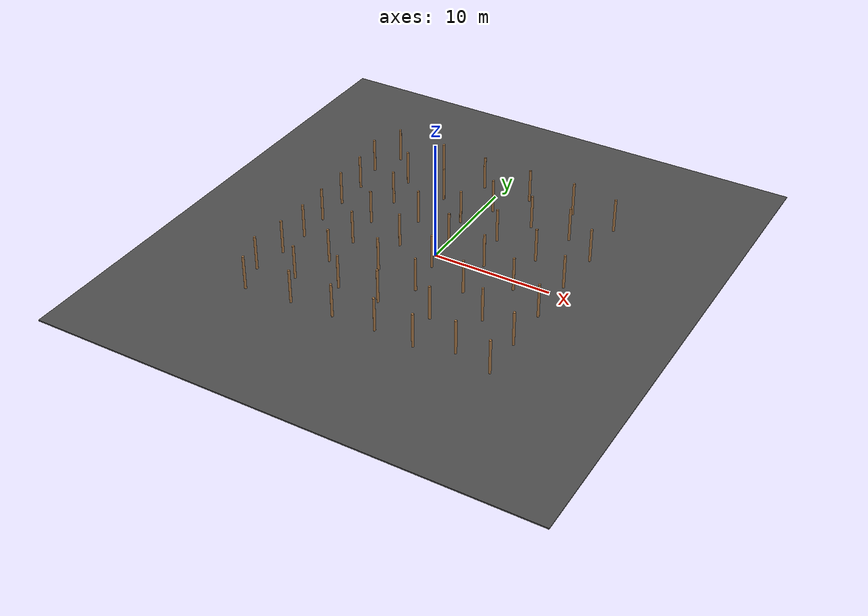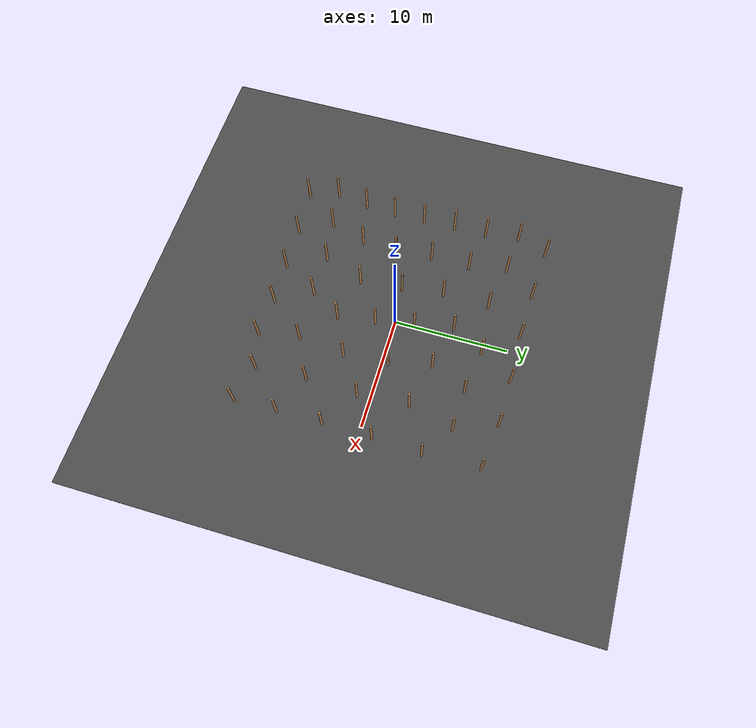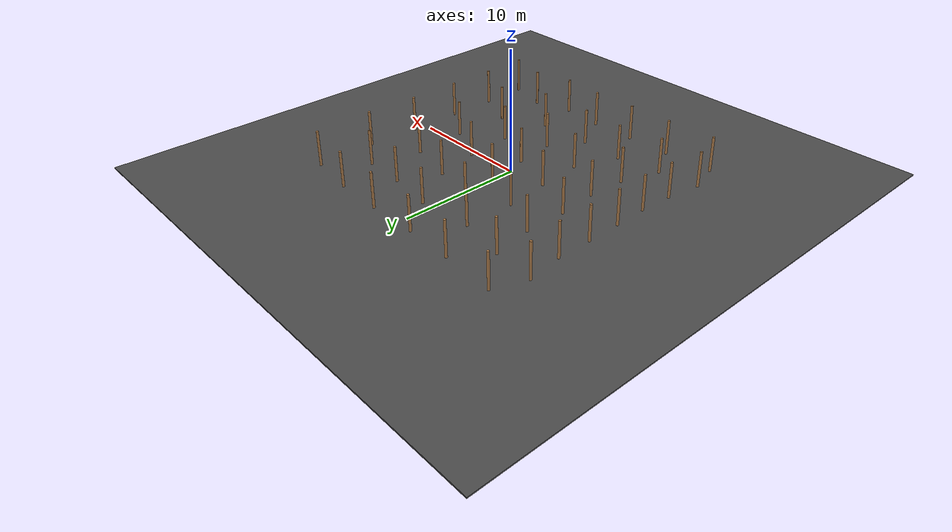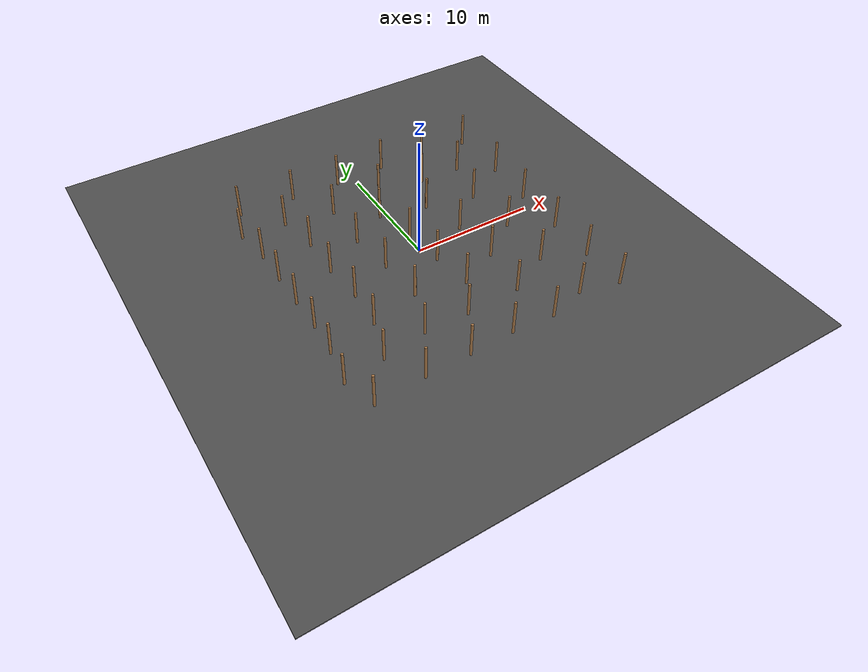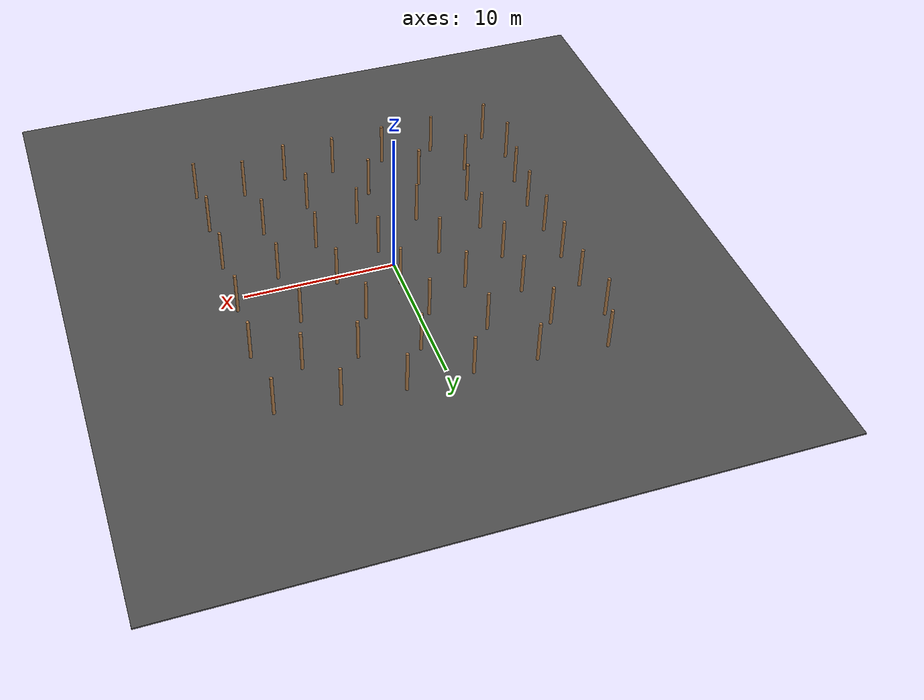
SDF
<sdf version="1.6">
 <world name="default">
  <light name="sun" type="directional">
   <pose>0 0 10 0 -0 0</pose>
   <diffuse>0.8 0.8 0.8 1</diffuse>
   <specular>0.1 0.1 0.1 1</specular>
   <attenuation>
    <range>1000</range>
    <constant>0.9</constant>
    <linear>0.01</linear>
    <quadratic>0.001</quadratic>
   </attenuation>
   <direction>-0.5 0.5 -1</direction>
  </light>
  <model name="asphalt_plane">
   <static>1</static>
   <link name="link">
    <collision name="collision"><geometry><box><size>42.4866 44.6464 0.1</size></box></geometry></collision>
    <visual name="visual">
     <cast_shadows>0</cast_shadows>
     <geometry><box><size>42.4866 44.6464 0.1</size></box></geometry>
     <material>
      <script>
       <uri>model://asphalt_plane/materials/scripts</uri>
       <uri>model://asphalt_plane/materials/textures</uri>
       <name>vrc/asphalt</name>
      </script>
     </material>
    </visual>
   </link>
  </model>
  <gravity>0 0 -9.8</gravity>
  <magnetic_field>6e-06 2.3e-05 -4.2e-05</magnetic_field>
  <atmosphere type="adiabatic"/>
  <physics name="default_physics" default="0" type="ode">
   <max_step_size>0.01</max_step_size>
   <real_time_factor>1</real_time_factor>
   <real_time_update_rate>100</real_time_update_rate>
  </physics>
  <scene><ambient>0.4 0.4 0.4 1</ambient><background>0.7 0.7 0.7 1</background><shadows>1</shadows></scene>
  <spherical_coordinates>
   <surface_model>EARTH_WGS84</surface_model>
   <latitude_deg>0</latitude_deg>
   <longitude_deg>0</longitude_deg>
   <elevation>0</elevation>
   <heading_deg>0</heading_deg>
  </spherical_coordinates>
  <model name="wooden_cylinder1_clone_0">
   <pose>-11.0868 8.52775 -6.1e-05 0 -0 0</pose>
   <link name="wooden_cylinder::link_0">
    <pose>0 0 1.5 0 -0 0</pose>
    <inertial>
     <mass>1</mass>
     <inertia><ixx>0.145833</ixx><ixy>0</ixy><ixz>0</ixz><iyy>0.145833</iyy><iyz>0</iyz><izz>0.125</izz></inertia>
    </inertial>
    <visual name="visual">
     <geometry><cylinder><radius>0.1</radius><length>3</length></cylinder></geometry>
     <material>
      <lighting>1</lighting>
      <script><uri>file://media/materials/scripts/gazebo.material</uri><name>Gazebo/Wood</name></script>
      <ambient>0.3 0.3 0.3 1</ambient>
      <diffuse>0.7 0.7 0.7 1</diffuse>
      <specular>0.01 0.01 0.01 1</specular>
      <emissive>0 0 0 1</emissive>
      <shader type="vertex"><normal_map>__default__</normal_map></shader>
     </material>
    </visual>
    <collision name="collision">
     <geometry><cylinder><radius>0.1</radius><length>3</length></cylinder></geometry>
     <surface>
      <friction>
       <ode><mu>1</mu><mu2>1</mu2><fdir1>0 0 0</fdir1><slip1>0</slip1><slip2>0</slip2></ode>
       <torsional>
        <coefficient>1</coefficient>
        <patch_radius>0</patch_radius>
        <surface_radius>0</surface_radius>
        <use_patch_radius>1</use_patch_radius>
        <ode><slip>0</slip></ode>
       </torsional>
      </friction>
      <bounce><restitution_coefficient>0</restitution_coefficient><threshold>1e+06</threshold></bounce>
      <contact>
       <collide_without_contact>0</collide_without_contact>
       <collide_without_contact_bitmask>1</collide_without_contact_bitmask>
       <collide_bitmask>1</collide_bitmask>
       <ode>
        <soft_cfm>0</soft_cfm>
        <soft_erp>0.2</soft_erp>
        <kp>1e+13</kp>
        <kd>1</kd>
        <max_vel>0.01</max_vel>
        <min_depth>0</min_depth>
       </ode>
       <bullet>
        <split_impulse>1</split_impulse>
        <split_impulse_penetration_threshold>-0.01</split_impulse_penetration_threshold>
        <soft_cfm>0</soft_cfm>
        <soft_erp>0.2</soft_erp>
        <kp>1e+13</kp>
        <kd>1</kd>
       </bullet>
      </contact>
     </surface>
    </collision>
   </link>
   <static>1</static>
  </model>
  <model name="wooden_cylinder1_clone_1">
   <pose>-10.642 2.62246 -6.3e-05 0 -0 0</pose>
   <link name="wooden_cylinder::link_0">
    <pose>0 0 1.5 0 -0 0</pose>
    <inertial>
     <mass>1</mass>
     <inertia><ixx>0.145833</ixx><ixy>0</ixy><ixz>0</ixz><iyy>0.145833</iyy><iyz>0</iyz><izz>0.125</izz></inertia>
    </inertial>
    <visual name="visual">
     <geometry><cylinder><radius>0.1</radius><length>3</length></cylinder></geometry>
     <material>
      <lighting>1</lighting>
      <script><uri>file://media/materials/scripts/gazebo.material</uri><name>Gazebo/Wood</name></script>
      <ambient>0.3 0.3 0.3 1</ambient>
      <diffuse>0.7 0.7 0.7 1</diffuse>
      <specular>0.01 0.01 0.01 1</specular>
      <emissive>0 0 0 1</emissive>
      <shader type="vertex"><normal_map>__default__</normal_map></shader>
     </material>
    </visual>
    <collision name="collision">
     <geometry><cylinder><radius>0.1</radius><length>3</length></cylinder></geometry>
     <surface>
      <friction>
       <ode><mu>1</mu><mu2>1</mu2><fdir1>0 0 0</fdir1><slip1>0</slip1><slip2>0</slip2></ode>
       <torsional>
        <coefficient>1</coefficient>
        <patch_radius>0</patch_radius>
        <surface_radius>0</surface_radius>
        <use_patch_radius>1</use_patch_radius>
        <ode><slip>0</slip></ode>
       </torsional>
      </friction>
      <bounce><restitution_coefficient>0</restitution_coefficient><threshold>1e+06</threshold></bounce>
      <contact>
       <collide_without_contact>0</collide_without_contact>
       <collide_without_contact_bitmask>1</collide_without_contact_bitmask>
       <collide_bitmask>1</collide_bitmask>
       <ode>
        <soft_cfm>0</soft_cfm>
        <soft_erp>0.2</soft_erp>
        <kp>1e+13</kp>
        <kd>1</kd>
        <max_vel>0.01</max_vel>
        <min_depth>0</min_depth>
       </ode>
       <bullet>
        <split_impulse>1</split_impulse>
        <split_impulse_penetration_threshold>-0.01</split_impulse_penetration_threshold>
        <soft_cfm>0</soft_cfm>
        <soft_erp>0.2</soft_erp>
        <kp>1e+13</kp>
        <kd>1</kd>
       </bullet>
      </contact>
     </surface>
    </collision>
   </link>
   <static>1</static>
  </model>
  <model name="wooden_cylinder1_clone_2">
   <pose>-10.6472 5.54644 0.000201 0 -0 0</pose>
   <link name="wooden_cylinder::link_0">
    <pose>0 0 1.5 0 -0 0</pose>
    <inertial>
     <mass>1</mass>
     <inertia><ixx>0.145833</ixx><ixy>0</ixy><ixz>0</ixz><iyy>0.145833</iyy><iyz>0</iyz><izz>0.125</izz></inertia>
    </inertial>
    <visual name="visual">
     <geometry><cylinder><radius>0.1</radius><length>3</length></cylinder></geometry>
     <material>
      <lighting>1</lighting>
      <script><uri>file://media/materials/scripts/gazebo.material</uri><name>Gazebo/Wood</name></script>
      <ambient>0.3 0.3 0.3 1</ambient>
      <diffuse>0.7 0.7 0.7 1</diffuse>
      <specular>0.01 0.01 0.01 1</specular>
      <emissive>0 0 0 1</emissive>
      <shader type="vertex"><normal_map>__default__</normal_map></shader>
     </material>
    </visual>
    <collision name="collision">
     <geometry><cylinder><radius>0.1</radius><length>3</length></cylinder></geometry>
     <surface>
      <friction>
       <ode><mu>1</mu><mu2>1</mu2><fdir1>0 0 0</fdir1><slip1>0</slip1><slip2>0</slip2></ode>
       <torsional>
        <coefficient>1</coefficient>
        <patch_radius>0</patch_radius>
        <surface_radius>0</surface_radius>
        <use_patch_radius>1</use_patch_radius>
        <ode><slip>0</slip></ode>
       </torsional>
      </friction>
      <bounce><restitution_coefficient>0</restitution_coefficient><threshold>1e+06</threshold></bounce>
      <contact>
       <collide_without_contact>0</collide_without_contact>
       <collide_without_contact_bitmask>1</collide_without_contact_bitmask>
       <collide_bitmask>1</collide_bitmask>
       <ode>
        <soft_cfm>0</soft_cfm>
        <soft_erp>0.2</soft_erp>
        <kp>1e+13</kp>
        <kd>1</kd>
        <max_vel>0.01</max_vel>
        <min_depth>0</min_depth>
       </ode>
       <bullet>
        <split_impulse>1</split_impulse>
        <split_impulse_penetration_threshold>-0.01</split_impulse_penetration_threshold>
        <soft_cfm>0</soft_cfm>
        <soft_erp>0.2</soft_erp>
        <kp>1e+13</kp>
        <kd>1</kd>
       </bullet>
      </contact>
     </surface>
    </collision>
   </link>
   <static>1</static>
  </model>
  <model name="wooden_cylinder1_clone_3">
   <pose>-10.5388 -3.0463 -0.000137 0 -0 0</pose>
   <link name="wooden_cylinder::link_0">
    <pose>0 0 1.5 0 -0 0</pose>
    <inertial>
     <mass>1</mass>
     <inertia><ixx>0.145833</ixx><ixy>0</ixy><ixz>0</ixz><iyy>0.145833</iyy><iyz>0</iyz><izz>0.125</izz></inertia>
    </inertial>
    <visual name="visual">
     <geometry><cylinder><radius>0.1</radius><length>3</length></cylinder></geometry>
     <material>
      <lighting>1</lighting>
      <script><uri>file://media/materials/scripts/gazebo.material</uri><name>Gazebo/Wood</name></script>
      <ambient>0.3 0.3 0.3 1</ambient>
      <diffuse>0.7 0.7 0.7 1</diffuse>
      <specular>0.01 0.01 0.01 1</specular>
      <emissive>0 0 0 1</emissive>
      <shader type="vertex"><normal_map>__default__</normal_map></shader>
     </material>
    </visual>
    <collision name="collision">
     <geometry><cylinder><radius>0.1</radius><length>3</length></cylinder></geometry>
     <surface>
      <friction>
       <ode><mu>1</mu><mu2>1</mu2><fdir1>0 0 0</fdir1><slip1>0</slip1><slip2>0</slip2></ode>
       <torsional>
        <coefficient>1</coefficient>
        <patch_radius>0</patch_radius>
        <surface_radius>0</surface_radius>
        <use_patch_radius>1</use_patch_radius>
        <ode><slip>0</slip></ode>
       </torsional>
      </friction>
      <bounce><restitution_coefficient>0</restitution_coefficient><threshold>1e+06</threshold></bounce>
      <contact>
       <collide_without_contact>0</collide_without_contact>
       <collide_without_contact_bitmask>1</collide_without_contact_bitmask>
       <collide_bitmask>1</collide_bitmask>
       <ode>
        <soft_cfm>0</soft_cfm>
        <soft_erp>0.2</soft_erp>
        <kp>1e+13</kp>
        <kd>1</kd>
        <max_vel>0.01</max_vel>
        <min_depth>0</min_depth>
       </ode>
       <bullet>
        <split_impulse>1</split_impulse>
        <split_impulse_penetration_threshold>-0.01</split_impulse_penetration_threshold>
        <soft_cfm>0</soft_cfm>
        <soft_erp>0.2</soft_erp>
        <kp>1e+13</kp>
        <kd>1</kd>
       </bullet>
      </contact>
     </surface>
    </collision>
   </link>
   <static>1</static>
  </model>
  <model name="wooden_cylinder1_clone_4">
   <pose>-10.6103 -0.27054 0.000102 0 -0 0</pose>
   <link name="wooden_cylinder::link_0">
    <pose>0 0 1.5 0 -0 0</pose>
    <inertial>
     <mass>1</mass>
     <inertia><ixx>0.145833</ixx><ixy>0</ixy><ixz>0</ixz><iyy>0.145833</iyy><iyz>0</iyz><izz>0.125</izz></inertia>
    </inertial>
    <visual name="visual">
     <geometry><cylinder><radius>0.1</radius><length>3</length></cylinder></geometry>
     <material>
      <lighting>1</lighting>
      <script><uri>file://media/materials/scripts/gazebo.material</uri><name>Gazebo/Wood</name></script>
      <ambient>0.3 0.3 0.3 1</ambient>
      <diffuse>0.7 0.7 0.7 1</diffuse>
      <specular>0.01 0.01 0.01 1</specular>
      <emissive>0 0 0 1</emissive>
      <shader type="vertex"><normal_map>__default__</normal_map></shader>
     </material>
    </visual>
    <collision name="collision">
     <geometry><cylinder><radius>0.1</radius><length>3</length></cylinder></geometry>
     <surface>
      <friction>
       <ode><mu>1</mu><mu2>1</mu2><fdir1>0 0 0</fdir1><slip1>0</slip1><slip2>0</slip2></ode>
       <torsional>
        <coefficient>1</coefficient>
        <patch_radius>0</patch_radius>
        <surface_radius>0</surface_radius>
        <use_patch_radius>1</use_patch_radius>
        <ode><slip>0</slip></ode>
       </torsional>
      </friction>
      <bounce><restitution_coefficient>0</restitution_coefficient><threshold>1e+06</threshold></bounce>
      <contact>
       <collide_without_contact>0</collide_without_contact>
       <collide_without_contact_bitmask>1</collide_without_contact_bitmask>
       <collide_bitmask>1</collide_bitmask>
       <ode>
        <soft_cfm>0</soft_cfm>
        <soft_erp>0.2</soft_erp>
        <kp>1e+13</kp>
        <kd>1</kd>
        <max_vel>0.01</max_vel>
        <min_depth>0</min_depth>
       </ode>
       <bullet>
        <split_impulse>1</split_impulse>
        <split_impulse_penetration_threshold>-0.01</split_impulse_penetration_threshold>
        <soft_cfm>0</soft_cfm>
        <soft_erp>0.2</soft_erp>
        <kp>1e+13</kp>
        <kd>1</kd>
       </bullet>
      </contact>
     </surface>
    </collision>
   </link>
   <static>1</static>
  </model>
  <model name="wooden_cylinder1_clone_5">
   <pose>-6.96669 1.43108 4.6e-05 0 -0 0</pose>
   <link name="wooden_cylinder::link_0">
    <pose>0 0 1.5 0 -0 0</pose>
    <inertial>
     <mass>1</mass>
     <inertia><ixx>0.145833</ixx><ixy>0</ixy><ixz>0</ixz><iyy>0.145833</iyy><iyz>0</iyz><izz>0.125</izz></inertia>
    </inertial>
    <visual name="visual">
     <geometry><cylinder><radius>0.1</radius><length>3</length></cylinder></geometry>
     <material>
      <lighting>1</lighting>
      <script><uri>file://media/materials/scripts/gazebo.material</uri><name>Gazebo/Wood</name></script>
      <ambient>0.3 0.3 0.3 1</ambient>
      <diffuse>0.7 0.7 0.7 1</diffuse>
      <specular>0.01 0.01 0.01 1</specular>
      <emissive>0 0 0 1</emissive>
      <shader type="vertex"><normal_map>__default__</normal_map></shader>
     </material>
    </visual>
    <collision name="collision">
     <geometry><cylinder><radius>0.1</radius><length>3</length></cylinder></geometry>
     <surface>
      <friction>
       <ode><mu>1</mu><mu2>1</mu2><fdir1>0 0 0</fdir1><slip1>0</slip1><slip2>0</slip2></ode>
       <torsional>
        <coefficient>1</coefficient>
        <patch_radius>0</patch_radius>
        <surface_radius>0</surface_radius>
        <use_patch_radius>1</use_patch_radius>
        <ode><slip>0</slip></ode>
       </torsional>
      </friction>
      <bounce><restitution_coefficient>0</restitution_coefficient><threshold>1e+06</threshold></bounce>
      <contact>
       <collide_without_contact>0</collide_without_contact>
       <collide_without_contact_bitmask>1</collide_without_contact_bitmask>
       <collide_bitmask>1</collide_bitmask>
       <ode>
        <soft_cfm>0</soft_cfm>
        <soft_erp>0.2</soft_erp>
        <kp>1e+13</kp>
        <kd>1</kd>
        <max_vel>0.01</max_vel>
        <min_depth>0</min_depth>
       </ode>
       <bullet>
        <split_impulse>1</split_impulse>
        <split_impulse_penetration_threshold>-0.01</split_impulse_penetration_threshold>
        <soft_cfm>0</soft_cfm>
        <soft_erp>0.2</soft_erp>
        <kp>1e+13</kp>
        <kd>1</kd>
       </bullet>
      </contact>
     </surface>
    </collision>
   </link>
   <static>1</static>
  </model>
  <model name="wooden_cylinder1_clone_6">
   <pose>-10.6948 -5.80428 7.4e-05 0 -0 0</pose>
   <link name="wooden_cylinder::link_0">
    <pose>0 0 1.5 0 -0 0</pose>
    <inertial>
     <mass>1</mass>
     <inertia><ixx>0.145833</ixx><ixy>0</ixy><ixz>0</ixz><iyy>0.145833</iyy><iyz>0</iyz><izz>0.125</izz></inertia>
    </inertial>
    <visual name="visual">
     <geometry><cylinder><radius>0.1</radius><length>3</length></cylinder></geometry>
     <material>
      <lighting>1</lighting>
      <script><uri>file://media/materials/scripts/gazebo.material</uri><name>Gazebo/Wood</name></script>
      <ambient>0.3 0.3 0.3 1</ambient>
      <diffuse>0.7 0.7 0.7 1</diffuse>
      <specular>0.01 0.01 0.01 1</specular>
      <emissive>0 0 0 1</emissive>
      <shader type="vertex"><normal_map>__default__</normal_map></shader>
     </material>
    </visual>
    <collision name="collision">
     <geometry><cylinder><radius>0.1</radius><length>3</length></cylinder></geometry>
     <surface>
      <friction>
       <ode><mu>1</mu><mu2>1</mu2><fdir1>0 0 0</fdir1><slip1>0</slip1><slip2>0</slip2></ode>
       <torsional>
        <coefficient>1</coefficient>
        <patch_radius>0</patch_radius>
        <surface_radius>0</surface_radius>
        <use_patch_radius>1</use_patch_radius>
        <ode><slip>0</slip></ode>
       </torsional>
      </friction>
      <bounce><restitution_coefficient>0</restitution_coefficient><threshold>1e+06</threshold></bounce>
      <contact>
       <collide_without_contact>0</collide_without_contact>
       <collide_without_contact_bitmask>1</collide_without_contact_bitmask>
       <collide_bitmask>1</collide_bitmask>
       <ode>
        <soft_cfm>0</soft_cfm>
        <soft_erp>0.2</soft_erp>
        <kp>1e+13</kp>
        <kd>1</kd>
        <max_vel>0.01</max_vel>
        <min_depth>0</min_depth>
       </ode>
       <bullet>
        <split_impulse>1</split_impulse>
        <split_impulse_penetration_threshold>-0.01</split_impulse_penetration_threshold>
        <soft_cfm>0</soft_cfm>
        <soft_erp>0.2</soft_erp>
        <kp>1e+13</kp>
        <kd>1</kd>
       </bullet>
      </contact>
     </surface>
    </collision>
   </link>
   <static>1</static>
  </model>
  <model name="wooden_cylinder1_clone_7">
   <pose>-6.8278 -4.97085 -0.000107 0 -0 0</pose>
   <link name="wooden_cylinder::link_0">
    <pose>0 0 1.5 0 -0 0</pose>
    <inertial>
     <mass>1</mass>
     <inertia><ixx>0.145833</ixx><ixy>0</ixy><ixz>0</ixz><iyy>0.145833</iyy><iyz>0</iyz><izz>0.125</izz></inertia>
    </inertial>
    <visual name="visual">
     <geometry><cylinder><radius>0.1</radius><length>3</length></cylinder></geometry>
     <material>
      <lighting>1</lighting>
      <script><uri>file://media/materials/scripts/gazebo.material</uri><name>Gazebo/Wood</name></script>
      <ambient>0.3 0.3 0.3 1</ambient>
      <diffuse>0.7 0.7 0.7 1</diffuse>
      <specular>0.01 0.01 0.01 1</specular>
      <emissive>0 0 0 1</emissive>
      <shader type="vertex"><normal_map>__default__</normal_map></shader>
     </material>
    </visual>
    <collision name="collision">
     <geometry><cylinder><radius>0.1</radius><length>3</length></cylinder></geometry>
     <surface>
      <friction>
       <ode><mu>1</mu><mu2>1</mu2><fdir1>0 0 0</fdir1><slip1>0</slip1><slip2>0</slip2></ode>
       <torsional>
        <coefficient>1</coefficient>
        <patch_radius>0</patch_radius>
        <surface_radius>0</surface_radius>
        <use_patch_radius>1</use_patch_radius>
        <ode><slip>0</slip></ode>
       </torsional>
      </friction>
      <bounce><restitution_coefficient>0</restitution_coefficient><threshold>1e+06</threshold></bounce>
      <contact>
       <collide_without_contact>0</collide_without_contact>
       <collide_without_contact_bitmask>1</collide_without_contact_bitmask>
       <collide_bitmask>1</collide_bitmask>
       <ode>
        <soft_cfm>0</soft_cfm>
        <soft_erp>0.2</soft_erp>
        <kp>1e+13</kp>
        <kd>1</kd>
        <max_vel>0.01</max_vel>
        <min_depth>0</min_depth>
       </ode>
       <bullet>
        <split_impulse>1</split_impulse>
        <split_impulse_penetration_threshold>-0.01</split_impulse_penetration_threshold>
        <soft_cfm>0</soft_cfm>
        <soft_erp>0.2</soft_erp>
        <kp>1e+13</kp>
        <kd>1</kd>
       </bullet>
      </contact>
     </surface>
    </collision>
   </link>
   <static>1</static>
  </model>
  <model name="wooden_cylinder1_clone_8">
   <pose>-6.64365 -1.83606 1e-06 0 -0 0</pose>
   <link name="wooden_cylinder::link_0">
    <pose>0 0 1.5 0 -0 0</pose>
    <inertial>
     <mass>1</mass>
     <inertia><ixx>0.145833</ixx><ixy>0</ixy><ixz>0</ixz><iyy>0.145833</iyy><iyz>0</iyz><izz>0.125</izz></inertia>
    </inertial>
    <visual name="visual">
     <geometry><cylinder><radius>0.1</radius><length>3</length></cylinder></geometry>
     <material>
      <lighting>1</lighting>
      <script><uri>file://media/materials/scripts/gazebo.material</uri><name>Gazebo/Wood</name></script>
      <ambient>0.3 0.3 0.3 1</ambient>
      <diffuse>0.7 0.7 0.7 1</diffuse>
      <specular>0.01 0.01 0.01 1</specular>
      <emissive>0 0 0 1</emissive>
      <shader type="vertex"><normal_map>__default__</normal_map></shader>
     </material>
    </visual>
    <collision name="collision">
     <geometry><cylinder><radius>0.1</radius><length>3</length></cylinder></geometry>
     <surface>
      <friction>
       <ode><mu>1</mu><mu2>1</mu2><fdir1>0 0 0</fdir1><slip1>0</slip1><slip2>0</slip2></ode>
       <torsional>
        <coefficient>1</coefficient>
        <patch_radius>0</patch_radius>
        <surface_radius>0</surface_radius>
        <use_patch_radius>1</use_patch_radius>
        <ode><slip>0</slip></ode>
       </torsional>
      </friction>
      <bounce><restitution_coefficient>0</restitution_coefficient><threshold>1e+06</threshold></bounce>
      <contact>
       <collide_without_contact>0</collide_without_contact>
       <collide_without_contact_bitmask>1</collide_without_contact_bitmask>
       <collide_bitmask>1</collide_bitmask>
       <ode>
        <soft_cfm>0</soft_cfm>
        <soft_erp>0.2</soft_erp>
        <kp>1e+13</kp>
        <kd>1</kd>
        <max_vel>0.01</max_vel>
        <min_depth>0</min_depth>
       </ode>
       <bullet>
        <split_impulse>1</split_impulse>
        <split_impulse_penetration_threshold>-0.01</split_impulse_penetration_threshold>
        <soft_cfm>0</soft_cfm>
        <soft_erp>0.2</soft_erp>
        <kp>1e+13</kp>
        <kd>1</kd>
       </bullet>
      </contact>
     </surface>
    </collision>
   </link>
   <static>1</static>
  </model>
  <model name="wooden_cylinder1_clone_9">
   <pose>-3.17556 -0.278555 4.8e-05 0 -0 0</pose>
   <link name="wooden_cylinder::link_0">
    <pose>0 0 1.5 0 -0 0</pose>
    <inertial>
     <mass>1</mass>
     <inertia><ixx>0.145833</ixx><ixy>0</ixy><ixz>0</ixz><iyy>0.145833</iyy><iyz>0</iyz><izz>0.125</izz></inertia>
    </inertial>
    <visual name="visual">
     <geometry><cylinder><radius>0.1</radius><length>3</length></cylinder></geometry>
     <material>
      <lighting>1</lighting>
      <script><uri>file://media/materials/scripts/gazebo.material</uri><name>Gazebo/Wood</name></script>
      <ambient>0.3 0.3 0.3 1</ambient>
      <diffuse>0.7 0.7 0.7 1</diffuse>
      <specular>0.01 0.01 0.01 1</specular>
      <emissive>0 0 0 1</emissive>
      <shader type="vertex"><normal_map>__default__</normal_map></shader>
     </material>
    </visual>
    <collision name="collision">
     <geometry><cylinder><radius>0.1</radius><length>3</length></cylinder></geometry>
     <surface>
      <friction>
       <ode><mu>1</mu><mu2>1</mu2><fdir1>0 0 0</fdir1><slip1>0</slip1><slip2>0</slip2></ode>
       <torsional>
        <coefficient>1</coefficient>
        <patch_radius>0</patch_radius>
        <surface_radius>0</surface_radius>
        <use_patch_radius>1</use_patch_radius>
        <ode><slip>0</slip></ode>
       </torsional>
      </friction>
      <bounce><restitution_coefficient>0</restitution_coefficient><threshold>1e+06</threshold></bounce>
      <contact>
       <collide_without_contact>0</collide_without_contact>
       <collide_without_contact_bitmask>1</collide_without_contact_bitmask>
       <collide_bitmask>1</collide_bitmask>
       <ode>
        <soft_cfm>0</soft_cfm>
        <soft_erp>0.2</soft_erp>
        <kp>1e+13</kp>
        <kd>1</kd>
        <max_vel>0.01</max_vel>
        <min_depth>0</min_depth>
       </ode>
       <bullet>
        <split_impulse>1</split_impulse>
        <split_impulse_penetration_threshold>-0.01</split_impulse_penetration_threshold>
        <soft_cfm>0</soft_cfm>
        <soft_erp>0.2</soft_erp>
        <kp>1e+13</kp>
        <kd>1</kd>
       </bullet>
      </contact>
     </surface>
    </collision>
   </link>
   <static>1</static>
  </model>
  <model name="wooden_cylinder1_clone_10">
   <pose>-11.1493 -8.66709 -8.7e-05 0 -0 0</pose>
   <link name="wooden_cylinder::link_0">
    <pose>0 0 1.5 0 -0 0</pose>
    <inertial>
     <mass>1</mass>
     <inertia><ixx>0.145833</ixx><ixy>0</ixy><ixz>0</ixz><iyy>0.145833</iyy><iyz>0</iyz><izz>0.125</izz></inertia>
    </inertial>
    <visual name="visual">
     <geometry><cylinder><radius>0.1</radius><length>3</length></cylinder></geometry>
     <material>
      <lighting>1</lighting>
      <script><uri>file://media/materials/scripts/gazebo.material</uri><name>Gazebo/Wood</name></script>
      <ambient>0.3 0.3 0.3 1</ambient>
      <diffuse>0.7 0.7 0.7 1</diffuse>
      <specular>0.01 0.01 0.01 1</specular>
      <emissive>0 0 0 1</emissive>
      <shader type="vertex"><normal_map>__default__</normal_map></shader>
     </material>
    </visual>
    <collision name="collision">
     <geometry><cylinder><radius>0.1</radius><length>3</length></cylinder></geometry>
     <surface>
      <friction>
       <ode><mu>1</mu><mu2>1</mu2><fdir1>0 0 0</fdir1><slip1>0</slip1><slip2>0</slip2></ode>
       <torsional>
        <coefficient>1</coefficient>
        <patch_radius>0</patch_radius>
        <surface_radius>0</surface_radius>
        <use_patch_radius>1</use_patch_radius>
        <ode><slip>0</slip></ode>
       </torsional>
      </friction>
      <bounce><restitution_coefficient>0</restitution_coefficient><threshold>1e+06</threshold></bounce>
      <contact>
       <collide_without_contact>0</collide_without_contact>
       <collide_without_contact_bitmask>1</collide_without_contact_bitmask>
       <collide_bitmask>1</collide_bitmask>
       <ode>
        <soft_cfm>0</soft_cfm>
        <soft_erp>0.2</soft_erp>
        <kp>1e+13</kp>
        <kd>1</kd>
        <max_vel>0.01</max_vel>
        <min_depth>0</min_depth>
       </ode>
       <bullet>
        <split_impulse>1</split_impulse>
        <split_impulse_penetration_threshold>-0.01</split_impulse_penetration_threshold>
        <soft_cfm>0</soft_cfm>
        <soft_erp>0.2</soft_erp>
        <kp>1e+13</kp>
        <kd>1</kd>
       </bullet>
      </contact>
     </surface>
    </collision>
   </link>
   <static>1</static>
  </model>
  <model name="wooden_cylinder1_clone_11">
   <pose>-4.23438 -7.57289 0.000132 0 -0 0</pose>
   <link name="wooden_cylinder::link_0">
    <pose>0 0 1.5 0 -0 0</pose>
    <inertial>
     <mass>1</mass>
     <inertia><ixx>0.145833</ixx><ixy>0</ixy><ixz>0</ixz><iyy>0.145833</iyy><iyz>0</iyz><izz>0.125</izz></inertia>
    </inertial>
    <visual name="visual">
     <geometry><cylinder><radius>0.1</radius><length>3</length></cylinder></geometry>
     <material>
      <lighting>1</lighting>
      <script><uri>file://media/materials/scripts/gazebo.material</uri><name>Gazebo/Wood</name></script>
      <ambient>0.3 0.3 0.3 1</ambient>
      <diffuse>0.7 0.7 0.7 1</diffuse>
      <specular>0.01 0.01 0.01 1</specular>
      <emissive>0 0 0 1</emissive>
      <shader type="vertex"><normal_map>__default__</normal_map></shader>
     </material>
    </visual>
    <collision name="collision">
     <geometry><cylinder><radius>0.1</radius><length>3</length></cylinder></geometry>
     <surface>
      <friction>
       <ode><mu>1</mu><mu2>1</mu2><fdir1>0 0 0</fdir1><slip1>0</slip1><slip2>0</slip2></ode>
       <torsional>
        <coefficient>1</coefficient>
        <patch_radius>0</patch_radius>
        <surface_radius>0</surface_radius>
        <use_patch_radius>1</use_patch_radius>
        <ode><slip>0</slip></ode>
       </torsional>
      </friction>
      <bounce><restitution_coefficient>0</restitution_coefficient><threshold>1e+06</threshold></bounce>
      <contact>
       <collide_without_contact>0</collide_without_contact>
       <collide_without_contact_bitmask>1</collide_without_contact_bitmask>
       <collide_bitmask>1</collide_bitmask>
       <ode>
        <soft_cfm>0</soft_cfm>
        <soft_erp>0.2</soft_erp>
        <kp>1e+13</kp>
        <kd>1</kd>
        <max_vel>0.01</max_vel>
        <min_depth>0</min_depth>
       </ode>
       <bullet>
        <split_impulse>1</split_impulse>
        <split_impulse_penetration_threshold>-0.01</split_impulse_penetration_threshold>
        <soft_cfm>0</soft_cfm>
        <soft_erp>0.2</soft_erp>
        <kp>1e+13</kp>
        <kd>1</kd>
       </bullet>
      </contact>
     </surface>
    </collision>
   </link>
   <static>1</static>
  </model>
  <model name="wooden_cylinder1_clone_12">
   <pose>1.05943 -4.89483 8e-06 0 -0 0</pose>
   <link name="wooden_cylinder::link_0">
    <pose>0 0 1.5 0 -0 0</pose>
    <inertial>
     <mass>1</mass>
     <inertia><ixx>0.145833</ixx><ixy>0</ixy><ixz>0</ixz><iyy>0.145833</iyy><iyz>0</iyz><izz>0.125</izz></inertia>
    </inertial>
    <visual name="visual">
     <geometry><cylinder><radius>0.1</radius><length>3</length></cylinder></geometry>
     <material>
      <lighting>1</lighting>
      <script><uri>file://media/materials/scripts/gazebo.material</uri><name>Gazebo/Wood</name></script>
      <ambient>0.3 0.3 0.3 1</ambient>
      <diffuse>0.7 0.7 0.7 1</diffuse>
      <specular>0.01 0.01 0.01 1</specular>
      <emissive>0 0 0 1</emissive>
      <shader type="vertex"><normal_map>__default__</normal_map></shader>
     </material>
    </visual>
    <collision name="collision">
     <geometry><cylinder><radius>0.1</radius><length>3</length></cylinder></geometry>
     <surface>
      <friction>
       <ode><mu>1</mu><mu2>1</mu2><fdir1>0 0 0</fdir1><slip1>0</slip1><slip2>0</slip2></ode>
       <torsional>
        <coefficient>1</coefficient>
        <patch_radius>0</patch_radius>
        <surface_radius>0</surface_radius>
        <use_patch_radius>1</use_patch_radius>
        <ode><slip>0</slip></ode>
       </torsional>
      </friction>
      <bounce><restitution_coefficient>0</restitution_coefficient><threshold>1e+06</threshold></bounce>
      <contact>
       <collide_without_contact>0</collide_without_contact>
       <collide_without_contact_bitmask>1</collide_without_contact_bitmask>
       <collide_bitmask>1</collide_bitmask>
       <ode>
        <soft_cfm>0</soft_cfm>
        <soft_erp>0.2</soft_erp>
        <kp>1e+13</kp>
        <kd>1</kd>
        <max_vel>0.01</max_vel>
        <min_depth>0</min_depth>
       </ode>
       <bullet>
        <split_impulse>1</split_impulse>
        <split_impulse_penetration_threshold>-0.01</split_impulse_penetration_threshold>
        <soft_cfm>0</soft_cfm>
        <soft_erp>0.2</soft_erp>
        <kp>1e+13</kp>
        <kd>1</kd>
       </bullet>
      </contact>
     </surface>
    </collision>
   </link>
   <static>1</static>
  </model>
  <model name="wooden_cylinder1_clone_13">
   <pose>-7.85705 -8.18766 1.7e-05 0 -0 0</pose>
   <link name="wooden_cylinder::link_0">
    <pose>0 0 1.5 0 -0 0</pose>
    <inertial>
     <mass>1</mass>
     <inertia><ixx>0.145833</ixx><ixy>0</ixy><ixz>0</ixz><iyy>0.145833</iyy><iyz>0</iyz><izz>0.125</izz></inertia>
    </inertial>
    <visual name="visual">
     <geometry><cylinder><radius>0.1</radius><length>3</length></cylinder></geometry>
     <material>
      <lighting>1</lighting>
      <script><uri>file://media/materials/scripts/gazebo.material</uri><name>Gazebo/Wood</name></script>
      <ambient>0.3 0.3 0.3 1</ambient>
      <diffuse>0.7 0.7 0.7 1</diffuse>
      <specular>0.01 0.01 0.01 1</specular>
      <emissive>0 0 0 1</emissive>
      <shader type="vertex"><normal_map>__default__</normal_map></shader>
     </material>
    </visual>
    <collision name="collision">
     <geometry><cylinder><radius>0.1</radius><length>3</length></cylinder></geometry>
     <surface>
      <friction>
       <ode><mu>1</mu><mu2>1</mu2><fdir1>0 0 0</fdir1><slip1>0</slip1><slip2>0</slip2></ode>
       <torsional>
        <coefficient>1</coefficient>
        <patch_radius>0</patch_radius>
        <surface_radius>0</surface_radius>
        <use_patch_radius>1</use_patch_radius>
        <ode><slip>0</slip></ode>
       </torsional>
      </friction>
      <bounce><restitution_coefficient>0</restitution_coefficient><threshold>1e+06</threshold></bounce>
      <contact>
       <collide_without_contact>0</collide_without_contact>
       <collide_without_contact_bitmask>1</collide_without_contact_bitmask>
       <collide_bitmask>1</collide_bitmask>
       <ode>
        <soft_cfm>0</soft_cfm>
        <soft_erp>0.2</soft_erp>
        <kp>1e+13</kp>
        <kd>1</kd>
        <max_vel>0.01</max_vel>
        <min_depth>0</min_depth>
       </ode>
       <bullet>
        <split_impulse>1</split_impulse>
        <split_impulse_penetration_threshold>-0.01</split_impulse_penetration_threshold>
        <soft_cfm>0</soft_cfm>
        <soft_erp>0.2</soft_erp>
        <kp>1e+13</kp>
        <kd>1</kd>
       </bullet>
      </contact>
     </surface>
    </collision>
   </link>
   <static>1</static>
  </model>
  <model name="wooden_cylinder1_clone_14">
   <pose>-0.619086 -7.63483 -3.8e-05 0 -0 0</pose>
   <link name="wooden_cylinder::link_0">
    <pose>0 0 1.5 0 -0 0</pose>
    <inertial>
     <mass>1</mass>
     <inertia><ixx>0.145833</ixx><ixy>0</ixy><ixz>0</ixz><iyy>0.145833</iyy><iyz>0</iyz><izz>0.125</izz></inertia>
    </inertial>
    <visual name="visual">
     <geometry><cylinder><radius>0.1</radius><length>3</length></cylinder></geometry>
     <material>
      <lighting>1</lighting>
      <script><uri>file://media/materials/scripts/gazebo.material</uri><name>Gazebo/Wood</name></script>
      <ambient>0.3 0.3 0.3 1</ambient>
      <diffuse>0.7 0.7 0.7 1</diffuse>
      <specular>0.01 0.01 0.01 1</specular>
      <emissive>0 0 0 1</emissive>
      <shader type="vertex"><normal_map>__default__</normal_map></shader>
     </material>
    </visual>
    <collision name="collision">
     <geometry><cylinder><radius>0.1</radius><length>3</length></cylinder></geometry>
     <surface>
      <friction>
       <ode><mu>1</mu><mu2>1</mu2><fdir1>0 0 0</fdir1><slip1>0</slip1><slip2>0</slip2></ode>
       <torsional>
        <coefficient>1</coefficient>
        <patch_radius>0</patch_radius>
        <surface_radius>0</surface_radius>
        <use_patch_radius>1</use_patch_radius>
        <ode><slip>0</slip></ode>
       </torsional>
      </friction>
      <bounce><restitution_coefficient>0</restitution_coefficient><threshold>1e+06</threshold></bounce>
      <contact>
       <collide_without_contact>0</collide_without_contact>
       <collide_without_contact_bitmask>1</collide_without_contact_bitmask>
       <collide_bitmask>1</collide_bitmask>
       <ode>
        <soft_cfm>0</soft_cfm>
        <soft_erp>0.2</soft_erp>
        <kp>1e+13</kp>
        <kd>1</kd>
        <max_vel>0.01</max_vel>
        <min_depth>0</min_depth>
       </ode>
       <bullet>
        <split_impulse>1</split_impulse>
        <split_impulse_penetration_threshold>-0.01</split_impulse_penetration_threshold>
        <soft_cfm>0</soft_cfm>
        <soft_erp>0.2</soft_erp>
        <kp>1e+13</kp>
        <kd>1</kd>
       </bullet>
      </contact>
     </surface>
    </collision>
   </link>
   <static>1</static>
  </model>
  <model name="wooden_cylinder1_clone_15">
   <pose>-6.29197 -11.0016 -2.7e-05 0 -0 0</pose>
   <link name="wooden_cylinder::link_0">
    <pose>0 0 1.5 0 -0 0</pose>
    <inertial>
     <mass>1</mass>
     <inertia><ixx>0.145833</ixx><ixy>0</ixy><ixz>0</ixz><iyy>0.145833</iyy><iyz>0</iyz><izz>0.125</izz></inertia>
    </inertial>
    <visual name="visual">
     <geometry><cylinder><radius>0.1</radius><length>3</length></cylinder></geometry>
     <material>
      <lighting>1</lighting>
      <script><uri>file://media/materials/scripts/gazebo.material</uri><name>Gazebo/Wood</name></script>
      <ambient>0.3 0.3 0.3 1</ambient>
      <diffuse>0.7 0.7 0.7 1</diffuse>
      <specular>0.01 0.01 0.01 1</specular>
      <emissive>0 0 0 1</emissive>
      <shader type="vertex"><normal_map>__default__</normal_map></shader>
     </material>
    </visual>
    <collision name="collision">
     <geometry><cylinder><radius>0.1</radius><length>3</length></cylinder></geometry>
     <surface>
      <friction>
       <ode><mu>1</mu><mu2>1</mu2><fdir1>0 0 0</fdir1><slip1>0</slip1><slip2>0</slip2></ode>
       <torsional>
        <coefficient>1</coefficient>
        <patch_radius>0</patch_radius>
        <surface_radius>0</surface_radius>
        <use_patch_radius>1</use_patch_radius>
        <ode><slip>0</slip></ode>
       </torsional>
      </friction>
      <bounce><restitution_coefficient>0</restitution_coefficient><threshold>1e+06</threshold></bounce>
      <contact>
       <collide_without_contact>0</collide_without_contact>
       <collide_without_contact_bitmask>1</collide_without_contact_bitmask>
       <collide_bitmask>1</collide_bitmask>
       <ode>
        <soft_cfm>0</soft_cfm>
        <soft_erp>0.2</soft_erp>
        <kp>1e+13</kp>
        <kd>1</kd>
        <max_vel>0.01</max_vel>
        <min_depth>0</min_depth>
       </ode>
       <bullet>
        <split_impulse>1</split_impulse>
        <split_impulse_penetration_threshold>-0.01</split_impulse_penetration_threshold>
        <soft_cfm>0</soft_cfm>
        <soft_erp>0.2</soft_erp>
        <kp>1e+13</kp>
        <kd>1</kd>
       </bullet>
      </contact>
     </surface>
    </collision>
   </link>
   <static>1</static>
  </model>
  <model name="wooden_cylinder1_clone_16">
   <pose>-2.60388 -10.8956 6.3e-05 0 -0 0</pose>
   <link name="wooden_cylinder::link_0">
    <pose>0 0 1.5 0 -0 0</pose>
    <inertial>
     <mass>1</mass>
     <inertia><ixx>0.145833</ixx><ixy>0</ixy><ixz>0</ixz><iyy>0.145833</iyy><iyz>0</iyz><izz>0.125</izz></inertia>
    </inertial>
    <visual name="visual">
     <geometry><cylinder><radius>0.1</radius><length>3</length></cylinder></geometry>
     <material>
      <lighting>1</lighting>
      <script><uri>file://media/materials/scripts/gazebo.material</uri><name>Gazebo/Wood</name></script>
      <ambient>0.3 0.3 0.3 1</ambient>
      <diffuse>0.7 0.7 0.7 1</diffuse>
      <specular>0.01 0.01 0.01 1</specular>
      <emissive>0 0 0 1</emissive>
      <shader type="vertex"><normal_map>__default__</normal_map></shader>
     </material>
    </visual>
    <collision name="collision">
     <geometry><cylinder><radius>0.1</radius><length>3</length></cylinder></geometry>
     <surface>
      <friction>
       <ode><mu>1</mu><mu2>1</mu2><fdir1>0 0 0</fdir1><slip1>0</slip1><slip2>0</slip2></ode>
       <torsional>
        <coefficient>1</coefficient>
        <patch_radius>0</patch_radius>
        <surface_radius>0</surface_radius>
        <use_patch_radius>1</use_patch_radius>
        <ode><slip>0</slip></ode>
       </torsional>
      </friction>
      <bounce><restitution_coefficient>0</restitution_coefficient><threshold>1e+06</threshold></bounce>
      <contact>
       <collide_without_contact>0</collide_without_contact>
       <collide_without_contact_bitmask>1</collide_without_contact_bitmask>
       <collide_bitmask>1</collide_bitmask>
       <ode>
        <soft_cfm>0</soft_cfm>
        <soft_erp>0.2</soft_erp>
        <kp>1e+13</kp>
        <kd>1</kd>
        <max_vel>0.01</max_vel>
        <min_depth>0</min_depth>
       </ode>
       <bullet>
        <split_impulse>1</split_impulse>
        <split_impulse_penetration_threshold>-0.01</split_impulse_penetration_threshold>
        <soft_cfm>0</soft_cfm>
        <soft_erp>0.2</soft_erp>
        <kp>1e+13</kp>
        <kd>1</kd>
       </bullet>
      </contact>
     </surface>
    </collision>
   </link>
   <static>1</static>
  </model>
  <model name="wooden_cylinder1_clone_17">
   <pose>-10.3374 -11.2731 -3e-05 0 -0 0</pose>
   <link name="wooden_cylinder::link_0">
    <pose>0 0 1.5 0 -0 0</pose>
    <inertial>
     <mass>1</mass>
     <inertia><ixx>0.145833</ixx><ixy>0</ixy><ixz>0</ixz><iyy>0.145833</iyy><iyz>0</iyz><izz>0.125</izz></inertia>
    </inertial>
    <visual name="visual">
     <geometry><cylinder><radius>0.1</radius><length>3</length></cylinder></geometry>
     <material>
      <lighting>1</lighting>
      <script><uri>file://media/materials/scripts/gazebo.material</uri><name>Gazebo/Wood</name></script>
      <ambient>0.3 0.3 0.3 1</ambient>
      <diffuse>0.7 0.7 0.7 1</diffuse>
      <specular>0.01 0.01 0.01 1</specular>
      <emissive>0 0 0 1</emissive>
      <shader type="vertex"><normal_map>__default__</normal_map></shader>
     </material>
    </visual>
    <collision name="collision">
     <geometry><cylinder><radius>0.1</radius><length>3</length></cylinder></geometry>
     <surface>
      <friction>
       <ode><mu>1</mu><mu2>1</mu2><fdir1>0 0 0</fdir1><slip1>0</slip1><slip2>0</slip2></ode>
       <torsional>
        <coefficient>1</coefficient>
        <patch_radius>0</patch_radius>
        <surface_radius>0</surface_radius>
        <use_patch_radius>1</use_patch_radius>
        <ode><slip>0</slip></ode>
       </torsional>
      </friction>
      <bounce><restitution_coefficient>0</restitution_coefficient><threshold>1e+06</threshold></bounce>
      <contact>
       <collide_without_contact>0</collide_without_contact>
       <collide_without_contact_bitmask>1</collide_without_contact_bitmask>
       <collide_bitmask>1</collide_bitmask>
       <ode>
        <soft_cfm>0</soft_cfm>
        <soft_erp>0.2</soft_erp>
        <kp>1e+13</kp>
        <kd>1</kd>
        <max_vel>0.01</max_vel>
        <min_depth>0</min_depth>
       </ode>
       <bullet>
        <split_impulse>1</split_impulse>
        <split_impulse_penetration_threshold>-0.01</split_impulse_penetration_threshold>
        <soft_cfm>0</soft_cfm>
        <soft_erp>0.2</soft_erp>
        <kp>1e+13</kp>
        <kd>1</kd>
       </bullet>
      </contact>
     </surface>
    </collision>
   </link>
   <static>1</static>
  </model>
  <model name="wooden_cylinder1_clone_18">
   <pose>1.05229 -10.7459 3e-05 0 -0 0</pose>
   <link name="wooden_cylinder::link_0">
    <pose>0 0 1.5 0 -0 0</pose>
    <inertial>
     <mass>1</mass>
     <inertia><ixx>0.145833</ixx><ixy>0</ixy><ixz>0</ixz><iyy>0.145833</iyy><iyz>0</iyz><izz>0.125</izz></inertia>
    </inertial>
    <visual name="visual">
     <geometry><cylinder><radius>0.1</radius><length>3</length></cylinder></geometry>
     <material>
      <lighting>1</lighting>
      <script><uri>file://media/materials/scripts/gazebo.material</uri><name>Gazebo/Wood</name></script>
      <ambient>0.3 0.3 0.3 1</ambient>
      <diffuse>0.7 0.7 0.7 1</diffuse>
      <specular>0.01 0.01 0.01 1</specular>
      <emissive>0 0 0 1</emissive>
      <shader type="vertex"><normal_map>__default__</normal_map></shader>
     </material>
    </visual>
    <collision name="collision">
     <geometry><cylinder><radius>0.1</radius><length>3</length></cylinder></geometry>
     <surface>
      <friction>
       <ode><mu>1</mu><mu2>1</mu2><fdir1>0 0 0</fdir1><slip1>0</slip1><slip2>0</slip2></ode>
       <torsional>
        <coefficient>1</coefficient>
        <patch_radius>0</patch_radius>
        <surface_radius>0</surface_radius>
        <use_patch_radius>1</use_patch_radius>
        <ode><slip>0</slip></ode>
       </torsional>
      </friction>
      <bounce><restitution_coefficient>0</restitution_coefficient><threshold>1e+06</threshold></bounce>
      <contact>
       <collide_without_contact>0</collide_without_contact>
       <collide_without_contact_bitmask>1</collide_without_contact_bitmask>
       <collide_bitmask>1</collide_bitmask>
       <ode>
        <soft_cfm>0</soft_cfm>
        <soft_erp>0.2</soft_erp>
        <kp>1e+13</kp>
        <kd>1</kd>
        <max_vel>0.01</max_vel>
        <min_depth>0</min_depth>
       </ode>
       <bullet>
        <split_impulse>1</split_impulse>
        <split_impulse_penetration_threshold>-0.01</split_impulse_penetration_threshold>
        <soft_cfm>0</soft_cfm>
        <soft_erp>0.2</soft_erp>
        <kp>1e+13</kp>
        <kd>1</kd>
       </bullet>
      </contact>
     </surface>
    </collision>
   </link>
   <static>1</static>
  </model>
  <model name="wooden_cylinder1_clone_19">
   <pose>7.54901 -10.0816 0.000231 0 -0 0</pose>
   <link name="wooden_cylinder::link_0">
    <pose>0 0 1.5 0 -0 0</pose>
    <inertial>
     <mass>1</mass>
     <inertia><ixx>0.145833</ixx><ixy>0</ixy><ixz>0</ixz><iyy>0.145833</iyy><iyz>0</iyz><izz>0.125</izz></inertia>
    </inertial>
    <visual name="visual">
     <geometry><cylinder><radius>0.1</radius><length>3</length></cylinder></geometry>
     <material>
      <lighting>1</lighting>
      <script><uri>file://media/materials/scripts/gazebo.material</uri><name>Gazebo/Wood</name></script>
      <ambient>0.3 0.3 0.3 1</ambient>
      <diffuse>0.7 0.7 0.7 1</diffuse>
      <specular>0.01 0.01 0.01 1</specular>
      <emissive>0 0 0 1</emissive>
      <shader type="vertex"><normal_map>__default__</normal_map></shader>
     </material>
    </visual>
    <collision name="collision">
     <geometry><cylinder><radius>0.1</radius><length>3</length></cylinder></geometry>
     <surface>
      <friction>
       <ode><mu>1</mu><mu2>1</mu2><fdir1>0 0 0</fdir1><slip1>0</slip1><slip2>0</slip2></ode>
       <torsional>
        <coefficient>1</coefficient>
        <patch_radius>0</patch_radius>
        <surface_radius>0</surface_radius>
        <use_patch_radius>1</use_patch_radius>
        <ode><slip>0</slip></ode>
       </torsional>
      </friction>
      <bounce><restitution_coefficient>0</restitution_coefficient><threshold>1e+06</threshold></bounce>
      <contact>
       <collide_without_contact>0</collide_without_contact>
       <collide_without_contact_bitmask>1</collide_without_contact_bitmask>
       <collide_bitmask>1</collide_bitmask>
       <ode>
        <soft_cfm>0</soft_cfm>
        <soft_erp>0.2</soft_erp>
        <kp>1e+13</kp>
        <kd>1</kd>
        <max_vel>0.01</max_vel>
        <min_depth>0</min_depth>
       </ode>
       <bullet>
        <split_impulse>1</split_impulse>
        <split_impulse_penetration_threshold>-0.01</split_impulse_penetration_threshold>
        <soft_cfm>0</soft_cfm>
        <soft_erp>0.2</soft_erp>
        <kp>1e+13</kp>
        <kd>1</kd>
       </bullet>
      </contact>
     </surface>
    </collision>
   </link>
   <static>1</static>
  </model>
  <model name="wooden_cylinder1_clone_20">
   <pose>3.82649 -7.44946 -9.6e-05 0 -0 0</pose>
   <link name="wooden_cylinder::link_0">
    <pose>0 0 1.5 0 -0 0</pose>
    <inertial>
     <mass>1</mass>
     <inertia><ixx>0.145833</ixx><ixy>0</ixy><ixz>0</ixz><iyy>0.145833</iyy><iyz>0</iyz><izz>0.125</izz></inertia>
    </inertial>
    <visual name="visual">
     <geometry><cylinder><radius>0.1</radius><length>3</length></cylinder></geometry>
     <material>
      <lighting>1</lighting>
      <script><uri>file://media/materials/scripts/gazebo.material</uri><name>Gazebo/Wood</name></script>
      <ambient>0.3 0.3 0.3 1</ambient>
      <diffuse>0.7 0.7 0.7 1</diffuse>
      <specular>0.01 0.01 0.01 1</specular>
      <emissive>0 0 0 1</emissive>
      <shader type="vertex"><normal_map>__default__</normal_map></shader>
     </material>
    </visual>
    <collision name="collision">
     <geometry><cylinder><radius>0.1</radius><length>3</length></cylinder></geometry>
     <surface>
      <friction>
       <ode><mu>1</mu><mu2>1</mu2><fdir1>0 0 0</fdir1><slip1>0</slip1><slip2>0</slip2></ode>
       <torsional>
        <coefficient>1</coefficient>
        <patch_radius>0</patch_radius>
        <surface_radius>0</surface_radius>
        <use_patch_radius>1</use_patch_radius>
        <ode><slip>0</slip></ode>
       </torsional>
      </friction>
      <bounce><restitution_coefficient>0</restitution_coefficient><threshold>1e+06</threshold></bounce>
      <contact>
       <collide_without_contact>0</collide_without_contact>
       <collide_without_contact_bitmask>1</collide_without_contact_bitmask>
       <collide_bitmask>1</collide_bitmask>
       <ode>
        <soft_cfm>0</soft_cfm>
        <soft_erp>0.2</soft_erp>
        <kp>1e+13</kp>
        <kd>1</kd>
        <max_vel>0.01</max_vel>
        <min_depth>0</min_depth>
       </ode>
       <bullet>
        <split_impulse>1</split_impulse>
        <split_impulse_penetration_threshold>-0.01</split_impulse_penetration_threshold>
        <soft_cfm>0</soft_cfm>
        <soft_erp>0.2</soft_erp>
        <kp>1e+13</kp>
        <kd>1</kd>
       </bullet>
      </contact>
     </surface>
    </collision>
   </link>
   <static>1</static>
  </model>
  <model name="wooden_cylinder1_clone_21">
   <pose>4.4732 -10.9726 0.000101 0 -0 0</pose>
   <link name="wooden_cylinder::link_0">
    <pose>0 0 1.5 0 -0 0</pose>
    <inertial>
     <mass>1</mass>
     <inertia><ixx>0.145833</ixx><ixy>0</ixy><ixz>0</ixz><iyy>0.145833</iyy><iyz>0</iyz><izz>0.125</izz></inertia>
    </inertial>
    <visual name="visual">
     <geometry><cylinder><radius>0.1</radius><length>3</length></cylinder></geometry>
     <material>
      <lighting>1</lighting>
      <script><uri>file://media/materials/scripts/gazebo.material</uri><name>Gazebo/Wood</name></script>
      <ambient>0.3 0.3 0.3 1</ambient>
      <diffuse>0.7 0.7 0.7 1</diffuse>
      <specular>0.01 0.01 0.01 1</specular>
      <emissive>0 0 0 1</emissive>
      <shader type="vertex"><normal_map>__default__</normal_map></shader>
     </material>
    </visual>
    <collision name="collision">
     <geometry><cylinder><radius>0.1</radius><length>3</length></cylinder></geometry>
     <surface>
      <friction>
       <ode><mu>1</mu><mu2>1</mu2><fdir1>0 0 0</fdir1><slip1>0</slip1><slip2>0</slip2></ode>
       <torsional>
        <coefficient>1</coefficient>
        <patch_radius>0</patch_radius>
        <surface_radius>0</surface_radius>
        <use_patch_radius>1</use_patch_radius>
        <ode><slip>0</slip></ode>
       </torsional>
      </friction>
      <bounce><restitution_coefficient>0</restitution_coefficient><threshold>1e+06</threshold></bounce>
      <contact>
       <collide_without_contact>0</collide_without_contact>
       <collide_without_contact_bitmask>1</collide_without_contact_bitmask>
       <collide_bitmask>1</collide_bitmask>
       <ode>
        <soft_cfm>0</soft_cfm>
        <soft_erp>0.2</soft_erp>
        <kp>1e+13</kp>
        <kd>1</kd>
        <max_vel>0.01</max_vel>
        <min_depth>0</min_depth>
       </ode>
       <bullet>
        <split_impulse>1</split_impulse>
        <split_impulse_penetration_threshold>-0.01</split_impulse_penetration_threshold>
        <soft_cfm>0</soft_cfm>
        <soft_erp>0.2</soft_erp>
        <kp>1e+13</kp>
        <kd>1</kd>
       </bullet>
      </contact>
     </surface>
    </collision>
   </link>
   <static>1</static>
  </model>
  <model name="wooden_cylinder1_clone_22">
   <pose>-2.86149 -4 -3.4e-05 0 -0 0</pose>
   <link name="wooden_cylinder::link_0">
    <pose>0 0 1.5 0 -0 0</pose>
    <inertial>
     <mass>1</mass>
     <inertia><ixx>0.145833</ixx><ixy>0</ixy><ixz>0</ixz><iyy>0.145833</iyy><iyz>0</iyz><izz>0.125</izz></inertia>
    </inertial>
    <visual name="visual">
     <geometry><cylinder><radius>0.1</radius><length>3</length></cylinder></geometry>
     <material>
      <lighting>1</lighting>
      <script><uri>file://media/materials/scripts/gazebo.material</uri><name>Gazebo/Wood</name></script>
      <ambient>0.3 0.3 0.3 1</ambient>
      <diffuse>0.7 0.7 0.7 1</diffuse>
      <specular>0.01 0.01 0.01 1</specular>
      <emissive>0 0 0 1</emissive>
      <shader type="vertex"><normal_map>__default__</normal_map></shader>
     </material>
    </visual>
    <collision name="collision">
     <geometry><cylinder><radius>0.1</radius><length>3</length></cylinder></geometry>
     <surface>
      <friction>
       <ode><mu>1</mu><mu2>1</mu2><fdir1>0 0 0</fdir1><slip1>0</slip1><slip2>0</slip2></ode>
       <torsional>
        <coefficient>1</coefficient>
        <patch_radius>0</patch_radius>
        <surface_radius>0</surface_radius>
        <use_patch_radius>1</use_patch_radius>
        <ode><slip>0</slip></ode>
       </torsional>
      </friction>
      <bounce><restitution_coefficient>0</restitution_coefficient><threshold>1e+06</threshold></bounce>
      <contact>
       <collide_without_contact>0</collide_without_contact>
       <collide_without_contact_bitmask>1</collide_without_contact_bitmask>
       <collide_bitmask>1</collide_bitmask>
       <ode>
        <soft_cfm>0</soft_cfm>
        <soft_erp>0.2</soft_erp>
        <kp>1e+13</kp>
        <kd>1</kd>
        <max_vel>0.01</max_vel>
        <min_depth>0</min_depth>
       </ode>
       <bullet>
        <split_impulse>1</split_impulse>
        <split_impulse_penetration_threshold>-0.01</split_impulse_penetration_threshold>
        <soft_cfm>0</soft_cfm>
        <soft_erp>0.2</soft_erp>
        <kp>1e+13</kp>
        <kd>1</kd>
       </bullet>
      </contact>
     </surface>
    </collision>
   </link>
   <static>1</static>
  </model>
  <model name="wooden_cylinder1_clone_23">
   <pose>4.35296 -3.31184 -0.000177 0 -0 0</pose>
   <link name="wooden_cylinder::link_0">
    <pose>0 0 1.5 0 -0 0</pose>
    <inertial>
     <mass>1</mass>
     <inertia><ixx>0.145833</ixx><ixy>0</ixy><ixz>0</ixz><iyy>0.145833</iyy><iyz>0</iyz><izz>0.125</izz></inertia>
    </inertial>
    <visual name="visual">
     <geometry><cylinder><radius>0.1</radius><length>3</length></cylinder></geometry>
     <material>
      <lighting>1</lighting>
      <script><uri>file://media/materials/scripts/gazebo.material</uri><name>Gazebo/Wood</name></script>
      <ambient>0.3 0.3 0.3 1</ambient>
      <diffuse>0.7 0.7 0.7 1</diffuse>
      <specular>0.01 0.01 0.01 1</specular>
      <emissive>0 0 0 1</emissive>
      <shader type="vertex"><normal_map>__default__</normal_map></shader>
     </material>
    </visual>
    <collision name="collision">
     <geometry><cylinder><radius>0.1</radius><length>3</length></cylinder></geometry>
     <surface>
      <friction>
       <ode><mu>1</mu><mu2>1</mu2><fdir1>0 0 0</fdir1><slip1>0</slip1><slip2>0</slip2></ode>
       <torsional>
        <coefficient>1</coefficient>
        <patch_radius>0</patch_radius>
        <surface_radius>0</surface_radius>
        <use_patch_radius>1</use_patch_radius>
        <ode><slip>0</slip></ode>
       </torsional>
      </friction>
      <bounce><restitution_coefficient>0</restitution_coefficient><threshold>1e+06</threshold></bounce>
      <contact>
       <collide_without_contact>0</collide_without_contact>
       <collide_without_contact_bitmask>1</collide_without_contact_bitmask>
       <collide_bitmask>1</collide_bitmask>
       <ode>
        <soft_cfm>0</soft_cfm>
        <soft_erp>0.2</soft_erp>
        <kp>1e+13</kp>
        <kd>1</kd>
        <max_vel>0.01</max_vel>
        <min_depth>0</min_depth>
       </ode>
       <bullet>
        <split_impulse>1</split_impulse>
        <split_impulse_penetration_threshold>-0.01</split_impulse_penetration_threshold>
        <soft_cfm>0</soft_cfm>
        <soft_erp>0.2</soft_erp>
        <kp>1e+13</kp>
        <kd>1</kd>
       </bullet>
      </contact>
     </surface>
    </collision>
   </link>
   <static>1</static>
  </model>
  <model name="wooden_cylinder1_clone_24">
   <pose>0.582381 -1.60032 7e-05 0 -0 0</pose>
   <link name="wooden_cylinder::link_0">
    <pose>0 0 1.5 0 -0 0</pose>
    <inertial>
     <mass>1</mass>
     <inertia><ixx>0.145833</ixx><ixy>0</ixy><ixz>0</ixz><iyy>0.145833</iyy><iyz>0</iyz><izz>0.125</izz></inertia>
    </inertial>
    <visual name="visual">
     <geometry><cylinder><radius>0.1</radius><length>3</length></cylinder></geometry>
     <material>
      <lighting>1</lighting>
      <script><uri>file://media/materials/scripts/gazebo.material</uri><name>Gazebo/Wood</name></script>
      <ambient>0.3 0.3 0.3 1</ambient>
      <diffuse>0.7 0.7 0.7 1</diffuse>
      <specular>0.01 0.01 0.01 1</specular>
      <emissive>0 0 0 1</emissive>
      <shader type="vertex"><normal_map>__default__</normal_map></shader>
     </material>
    </visual>
    <collision name="collision">
     <geometry><cylinder><radius>0.1</radius><length>3</length></cylinder></geometry>
     <surface>
      <friction>
       <ode><mu>1</mu><mu2>1</mu2><fdir1>0 0 0</fdir1><slip1>0</slip1><slip2>0</slip2></ode>
       <torsional>
        <coefficient>1</coefficient>
        <patch_radius>0</patch_radius>
        <surface_radius>0</surface_radius>
        <use_patch_radius>1</use_patch_radius>
        <ode><slip>0</slip></ode>
       </torsional>
      </friction>
      <bounce><restitution_coefficient>0</restitution_coefficient><threshold>1e+06</threshold></bounce>
      <contact>
       <collide_without_contact>0</collide_without_contact>
       <collide_without_contact_bitmask>1</collide_without_contact_bitmask>
       <collide_bitmask>1</collide_bitmask>
       <ode>
        <soft_cfm>0</soft_cfm>
        <soft_erp>0.2</soft_erp>
        <kp>1e+13</kp>
        <kd>1</kd>
        <max_vel>0.01</max_vel>
        <min_depth>0</min_depth>
       </ode>
       <bullet>
        <split_impulse>1</split_impulse>
        <split_impulse_penetration_threshold>-0.01</split_impulse_penetration_threshold>
        <soft_cfm>0</soft_cfm>
        <soft_erp>0.2</soft_erp>
        <kp>1e+13</kp>
        <kd>1</kd>
       </bullet>
      </contact>
     </surface>
    </collision>
   </link>
   <static>1</static>
  </model>
  <model name="wooden_cylinder1_clone_25">
   <pose>7.31258 -5.66031 -0.000174 0 -0 0</pose>
   <link name="wooden_cylinder::link_0">
    <pose>0 0 1.5 0 -0 0</pose>
    <inertial>
     <mass>1</mass>
     <inertia><ixx>0.145833</ixx><ixy>0</ixy><ixz>0</ixz><iyy>0.145833</iyy><iyz>0</iyz><izz>0.125</izz></inertia>
    </inertial>
    <visual name="visual">
     <geometry><cylinder><radius>0.1</radius><length>3</length></cylinder></geometry>
     <material>
      <lighting>1</lighting>
      <script><uri>file://media/materials/scripts/gazebo.material</uri><name>Gazebo/Wood</name></script>
      <ambient>0.3 0.3 0.3 1</ambient>
      <diffuse>0.7 0.7 0.7 1</diffuse>
      <specular>0.01 0.01 0.01 1</specular>
      <emissive>0 0 0 1</emissive>
      <shader type="vertex"><normal_map>__default__</normal_map></shader>
     </material>
    </visual>
    <collision name="collision">
     <geometry><cylinder><radius>0.1</radius><length>3</length></cylinder></geometry>
     <surface>
      <friction>
       <ode><mu>1</mu><mu2>1</mu2><fdir1>0 0 0</fdir1><slip1>0</slip1><slip2>0</slip2></ode>
       <torsional>
        <coefficient>1</coefficient>
        <patch_radius>0</patch_radius>
        <surface_radius>0</surface_radius>
        <use_patch_radius>1</use_patch_radius>
        <ode><slip>0</slip></ode>
       </torsional>
      </friction>
      <bounce><restitution_coefficient>0</restitution_coefficient><threshold>1e+06</threshold></bounce>
      <contact>
       <collide_without_contact>0</collide_without_contact>
       <collide_without_contact_bitmask>1</collide_without_contact_bitmask>
       <collide_bitmask>1</collide_bitmask>
       <ode>
        <soft_cfm>0</soft_cfm>
        <soft_erp>0.2</soft_erp>
        <kp>1e+13</kp>
        <kd>1</kd>
        <max_vel>0.01</max_vel>
        <min_depth>0</min_depth>
       </ode>
       <bullet>
        <split_impulse>1</split_impulse>
        <split_impulse_penetration_threshold>-0.01</split_impulse_penetration_threshold>
        <soft_cfm>0</soft_cfm>
        <soft_erp>0.2</soft_erp>
        <kp>1e+13</kp>
        <kd>1</kd>
       </bullet>
      </contact>
     </surface>
    </collision>
   </link>
   <static>1</static>
  </model>
  <model name="wooden_cylinder1_clone_26">
   <pose>0.175606 1.77763 6.1e-05 0 -0 0</pose>
   <link name="wooden_cylinder::link_0">
    <pose>0 0 1.5 0 -0 0</pose>
    <inertial>
     <mass>1</mass>
     <inertia><ixx>0.145833</ixx><ixy>0</ixy><ixz>0</ixz><iyy>0.145833</iyy><iyz>0</iyz><izz>0.125</izz></inertia>
    </inertial>
    <visual name="visual">
     <geometry><cylinder><radius>0.1</radius><length>3</length></cylinder></geometry>
     <material>
      <lighting>1</lighting>
      <script><uri>file://media/materials/scripts/gazebo.material</uri><name>Gazebo/Wood</name></script>
      <ambient>0.3 0.3 0.3 1</ambient>
      <diffuse>0.7 0.7 0.7 1</diffuse>
      <specular>0.01 0.01 0.01 1</specular>
      <emissive>0 0 0 1</emissive>
      <shader type="vertex"><normal_map>__default__</normal_map></shader>
     </material>
    </visual>
    <collision name="collision">
     <geometry><cylinder><radius>0.1</radius><length>3</length></cylinder></geometry>
     <surface>
      <friction>
       <ode><mu>1</mu><mu2>1</mu2><fdir1>0 0 0</fdir1><slip1>0</slip1><slip2>0</slip2></ode>
       <torsional>
        <coefficient>1</coefficient>
        <patch_radius>0</patch_radius>
        <surface_radius>0</surface_radius>
        <use_patch_radius>1</use_patch_radius>
        <ode><slip>0</slip></ode>
       </torsional>
      </friction>
      <bounce><restitution_coefficient>0</restitution_coefficient><threshold>1e+06</threshold></bounce>
      <contact>
       <collide_without_contact>0</collide_without_contact>
       <collide_without_contact_bitmask>1</collide_without_contact_bitmask>
       <collide_bitmask>1</collide_bitmask>
       <ode>
        <soft_cfm>0</soft_cfm>
        <soft_erp>0.2</soft_erp>
        <kp>1e+13</kp>
        <kd>1</kd>
        <max_vel>0.01</max_vel>
        <min_depth>0</min_depth>
       </ode>
       <bullet>
        <split_impulse>1</split_impulse>
        <split_impulse_penetration_threshold>-0.01</split_impulse_penetration_threshold>
        <soft_cfm>0</soft_cfm>
        <soft_erp>0.2</soft_erp>
        <kp>1e+13</kp>
        <kd>1</kd>
       </bullet>
      </contact>
     </surface>
    </collision>
   </link>
   <static>1</static>
  </model>
  <model name="wooden_cylinder1_clone_27">
   <pose>-3.64792 3.38842 4.1e-05 0 -0 0</pose>
   <link name="wooden_cylinder::link_0">
    <pose>0 0 1.5 0 -0 0</pose>
    <inertial>
     <mass>1</mass>
     <inertia><ixx>0.145833</ixx><ixy>0</ixy><ixz>0</ixz><iyy>0.145833</iyy><iyz>0</iyz><izz>0.125</izz></inertia>
    </inertial>
    <visual name="visual">
     <geometry><cylinder><radius>0.1</radius><length>3</length></cylinder></geometry>
     <material>
      <lighting>1</lighting>
      <script><uri>file://media/materials/scripts/gazebo.material</uri><name>Gazebo/Wood</name></script>
      <ambient>0.3 0.3 0.3 1</ambient>
      <diffuse>0.7 0.7 0.7 1</diffuse>
      <specular>0.01 0.01 0.01 1</specular>
      <emissive>0 0 0 1</emissive>
      <shader type="vertex"><normal_map>__default__</normal_map></shader>
     </material>
    </visual>
    <collision name="collision">
     <geometry><cylinder><radius>0.1</radius><length>3</length></cylinder></geometry>
     <surface>
      <friction>
       <ode><mu>1</mu><mu2>1</mu2><fdir1>0 0 0</fdir1><slip1>0</slip1><slip2>0</slip2></ode>
       <torsional>
        <coefficient>1</coefficient>
        <patch_radius>0</patch_radius>
        <surface_radius>0</surface_radius>
        <use_patch_radius>1</use_patch_radius>
        <ode><slip>0</slip></ode>
       </torsional>
      </friction>
      <bounce><restitution_coefficient>0</restitution_coefficient><threshold>1e+06</threshold></bounce>
      <contact>
       <collide_without_contact>0</collide_without_contact>
       <collide_without_contact_bitmask>1</collide_without_contact_bitmask>
       <collide_bitmask>1</collide_bitmask>
       <ode>
        <soft_cfm>0</soft_cfm>
        <soft_erp>0.2</soft_erp>
        <kp>1e+13</kp>
        <kd>1</kd>
        <max_vel>0.01</max_vel>
        <min_depth>0</min_depth>
       </ode>
       <bullet>
        <split_impulse>1</split_impulse>
        <split_impulse_penetration_threshold>-0.01</split_impulse_penetration_threshold>
        <soft_cfm>0</soft_cfm>
        <soft_erp>0.2</soft_erp>
        <kp>1e+13</kp>
        <kd>1</kd>
       </bullet>
      </contact>
     </surface>
    </collision>
   </link>
   <static>1</static>
  </model>
  <model name="wooden_cylinder1_clone_28">
   <pose>10.6822 -7.09279 -0.000131 0 -0 0</pose>
   <link name="wooden_cylinder::link_0">
    <pose>0 0 1.5 0 -0 0</pose>
    <inertial>
     <mass>1</mass>
     <inertia><ixx>0.145833</ixx><ixy>0</ixy><ixz>0</ixz><iyy>0.145833</iyy><iyz>0</iyz><izz>0.125</izz></inertia>
    </inertial>
    <visual name="visual">
     <geometry><cylinder><radius>0.1</radius><length>3</length></cylinder></geometry>
     <material>
      <lighting>1</lighting>
      <script><uri>file://media/materials/scripts/gazebo.material</uri><name>Gazebo/Wood</name></script>
      <ambient>0.3 0.3 0.3 1</ambient>
      <diffuse>0.7 0.7 0.7 1</diffuse>
      <specular>0.01 0.01 0.01 1</specular>
      <emissive>0 0 0 1</emissive>
      <shader type="vertex"><normal_map>__default__</normal_map></shader>
     </material>
    </visual>
    <collision name="collision">
     <geometry><cylinder><radius>0.1</radius><length>3</length></cylinder></geometry>
     <surface>
      <friction>
       <ode><mu>1</mu><mu2>1</mu2><fdir1>0 0 0</fdir1><slip1>0</slip1><slip2>0</slip2></ode>
       <torsional>
        <coefficient>1</coefficient>
        <patch_radius>0</patch_radius>
        <surface_radius>0</surface_radius>
        <use_patch_radius>1</use_patch_radius>
        <ode><slip>0</slip></ode>
       </torsional>
      </friction>
      <bounce><restitution_coefficient>0</restitution_coefficient><threshold>1e+06</threshold></bounce>
      <contact>
       <collide_without_contact>0</collide_without_contact>
       <collide_without_contact_bitmask>1</collide_without_contact_bitmask>
       <collide_bitmask>1</collide_bitmask>
       <ode>
        <soft_cfm>0</soft_cfm>
        <soft_erp>0.2</soft_erp>
        <kp>1e+13</kp>
        <kd>1</kd>
        <max_vel>0.01</max_vel>
        <min_depth>0</min_depth>
       </ode>
       <bullet>
        <split_impulse>1</split_impulse>
        <split_impulse_penetration_threshold>-0.01</split_impulse_penetration_threshold>
        <soft_cfm>0</soft_cfm>
        <soft_erp>0.2</soft_erp>
        <kp>1e+13</kp>
        <kd>1</kd>
       </bullet>
      </contact>
     </surface>
    </collision>
   </link>
   <static>1</static>
  </model>
  <model name="wooden_cylinder1_clone_29">
   <pose>-6.93659 4.8959 2e-05 0 -0 0</pose>
   <link name="wooden_cylinder::link_0">
    <pose>0 0 1.5 0 -0 0</pose>
    <inertial>
     <mass>1</mass>
     <inertia><ixx>0.145833</ixx><ixy>0</ixy><ixz>0</ixz><iyy>0.145833</iyy><iyz>0</iyz><izz>0.125</izz></inertia>
    </inertial>
    <visual name="visual">
     <geometry><cylinder><radius>0.1</radius><length>3</length></cylinder></geometry>
     <material>
      <lighting>1</lighting>
      <script><uri>file://media/materials/scripts/gazebo.material</uri><name>Gazebo/Wood</name></script>
      <ambient>0.3 0.3 0.3 1</ambient>
      <diffuse>0.7 0.7 0.7 1</diffuse>
      <specular>0.01 0.01 0.01 1</specular>
      <emissive>0 0 0 1</emissive>
      <shader type="vertex"><normal_map>__default__</normal_map></shader>
     </material>
    </visual>
    <collision name="collision">
     <geometry><cylinder><radius>0.1</radius><length>3</length></cylinder></geometry>
     <surface>
      <friction>
       <ode><mu>1</mu><mu2>1</mu2><fdir1>0 0 0</fdir1><slip1>0</slip1><slip2>0</slip2></ode>
       <torsional>
        <coefficient>1</coefficient>
        <patch_radius>0</patch_radius>
        <surface_radius>0</surface_radius>
        <use_patch_radius>1</use_patch_radius>
        <ode><slip>0</slip></ode>
       </torsional>
      </friction>
      <bounce><restitution_coefficient>0</restitution_coefficient><threshold>1e+06</threshold></bounce>
      <contact>
       <collide_without_contact>0</collide_without_contact>
       <collide_without_contact_bitmask>1</collide_without_contact_bitmask>
       <collide_bitmask>1</collide_bitmask>
       <ode>
        <soft_cfm>0</soft_cfm>
        <soft_erp>0.2</soft_erp>
        <kp>1e+13</kp>
        <kd>1</kd>
        <max_vel>0.01</max_vel>
        <min_depth>0</min_depth>
       </ode>
       <bullet>
        <split_impulse>1</split_impulse>
        <split_impulse_penetration_threshold>-0.01</split_impulse_penetration_threshold>
        <soft_cfm>0</soft_cfm>
        <soft_erp>0.2</soft_erp>
        <kp>1e+13</kp>
        <kd>1</kd>
       </bullet>
      </contact>
     </surface>
    </collision>
   </link>
   <static>1</static>
  </model>
  <model name="wooden_cylinder1_clone_30">
   <pose>4.04798 0.554378 8.8e-05 0 -0 0</pose>
   <link name="wooden_cylinder::link_0">
    <pose>0 0 1.5 0 -0 0</pose>
    <inertial>
     <mass>1</mass>
     <inertia><ixx>0.145833</ixx><ixy>0</ixy><ixz>0</ixz><iyy>0.145833</iyy><iyz>0</iyz><izz>0.125</izz></inertia>
    </inertial>
    <visual name="visual">
     <geometry><cylinder><radius>0.1</radius><length>3</length></cylinder></geometry>
     <material>
      <lighting>1</lighting>
      <script><uri>file://media/materials/scripts/gazebo.material</uri><name>Gazebo/Wood</name></script>
      <ambient>0.3 0.3 0.3 1</ambient>
      <diffuse>0.7 0.7 0.7 1</diffuse>
      <specular>0.01 0.01 0.01 1</specular>
      <emissive>0 0 0 1</emissive>
      <shader type="vertex"><normal_map>__default__</normal_map></shader>
     </material>
    </visual>
    <collision name="collision">
     <geometry><cylinder><radius>0.1</radius><length>3</length></cylinder></geometry>
     <surface>
      <friction>
       <ode><mu>1</mu><mu2>1</mu2><fdir1>0 0 0</fdir1><slip1>0</slip1><slip2>0</slip2></ode>
       <torsional>
        <coefficient>1</coefficient>
        <patch_radius>0</patch_radius>
        <surface_radius>0</surface_radius>
        <use_patch_radius>1</use_patch_radius>
        <ode><slip>0</slip></ode>
       </torsional>
      </friction>
      <bounce><restitution_coefficient>0</restitution_coefficient><threshold>1e+06</threshold></bounce>
      <contact>
       <collide_without_contact>0</collide_without_contact>
       <collide_without_contact_bitmask>1</collide_without_contact_bitmask>
       <collide_bitmask>1</collide_bitmask>
       <ode>
        <soft_cfm>0</soft_cfm>
        <soft_erp>0.2</soft_erp>
        <kp>1e+13</kp>
        <kd>1</kd>
        <max_vel>0.01</max_vel>
        <min_depth>0</min_depth>
       </ode>
       <bullet>
        <split_impulse>1</split_impulse>
        <split_impulse_penetration_threshold>-0.01</split_impulse_penetration_threshold>
        <soft_cfm>0</soft_cfm>
        <soft_erp>0.2</soft_erp>
        <kp>1e+13</kp>
        <kd>1</kd>
       </bullet>
      </contact>
     </surface>
    </collision>
   </link>
   <static>1</static>
  </model>
  <model name="wooden_cylinder1_clone_31">
   <pose>-7.54136 8.21907 -8.2e-05 0 -0 0</pose>
   <link name="wooden_cylinder::link_0">
    <pose>0 0 1.5 0 -0 0</pose>
    <inertial>
     <mass>1</mass>
     <inertia><ixx>0.145833</ixx><ixy>0</ixy><ixz>0</ixz><iyy>0.145833</iyy><iyz>0</iyz><izz>0.125</izz></inertia>
    </inertial>
    <visual name="visual">
     <geometry><cylinder><radius>0.1</radius><length>3</length></cylinder></geometry>
     <material>
      <lighting>1</lighting>
      <script><uri>file://media/materials/scripts/gazebo.material</uri><name>Gazebo/Wood</name></script>
      <ambient>0.3 0.3 0.3 1</ambient>
      <diffuse>0.7 0.7 0.7 1</diffuse>
      <specular>0.01 0.01 0.01 1</specular>
      <emissive>0 0 0 1</emissive>
      <shader type="vertex"><normal_map>__default__</normal_map></shader>
     </material>
    </visual>
    <collision name="collision">
     <geometry><cylinder><radius>0.1</radius><length>3</length></cylinder></geometry>
     <surface>
      <friction>
       <ode><mu>1</mu><mu2>1</mu2><fdir1>0 0 0</fdir1><slip1>0</slip1><slip2>0</slip2></ode>
       <torsional>
        <coefficient>1</coefficient>
        <patch_radius>0</patch_radius>
        <surface_radius>0</surface_radius>
        <use_patch_radius>1</use_patch_radius>
        <ode><slip>0</slip></ode>
       </torsional>
      </friction>
      <bounce><restitution_coefficient>0</restitution_coefficient><threshold>1e+06</threshold></bounce>
      <contact>
       <collide_without_contact>0</collide_without_contact>
       <collide_without_contact_bitmask>1</collide_without_contact_bitmask>
       <collide_bitmask>1</collide_bitmask>
       <ode>
        <soft_cfm>0</soft_cfm>
        <soft_erp>0.2</soft_erp>
        <kp>1e+13</kp>
        <kd>1</kd>
        <max_vel>0.01</max_vel>
        <min_depth>0</min_depth>
       </ode>
       <bullet>
        <split_impulse>1</split_impulse>
        <split_impulse_penetration_threshold>-0.01</split_impulse_penetration_threshold>
        <soft_cfm>0</soft_cfm>
        <soft_erp>0.2</soft_erp>
        <kp>1e+13</kp>
        <kd>1</kd>
       </bullet>
      </contact>
     </surface>
    </collision>
   </link>
   <static>1</static>
  </model>
  <model name="wooden_cylinder1_clone_32">
   <pose>7.50706 -1.09907 2.9e-05 0 -0 0</pose>
   <link name="wooden_cylinder::link_0">
    <pose>0 0 1.5 0 -0 0</pose>
    <inertial>
     <mass>1</mass>
     <inertia><ixx>0.145833</ixx><ixy>0</ixy><ixz>0</ixz><iyy>0.145833</iyy><iyz>0</iyz><izz>0.125</izz></inertia>
    </inertial>
    <visual name="visual">
     <geometry><cylinder><radius>0.1</radius><length>3</length></cylinder></geometry>
     <material>
      <lighting>1</lighting>
      <script><uri>file://media/materials/scripts/gazebo.material</uri><name>Gazebo/Wood</name></script>
      <ambient>0.3 0.3 0.3 1</ambient>
      <diffuse>0.7 0.7 0.7 1</diffuse>
      <specular>0.01 0.01 0.01 1</specular>
      <emissive>0 0 0 1</emissive>
      <shader type="vertex"><normal_map>__default__</normal_map></shader>
     </material>
    </visual>
    <collision name="collision">
     <geometry><cylinder><radius>0.1</radius><length>3</length></cylinder></geometry>
     <surface>
      <friction>
       <ode><mu>1</mu><mu2>1</mu2><fdir1>0 0 0</fdir1><slip1>0</slip1><slip2>0</slip2></ode>
       <torsional>
        <coefficient>1</coefficient>
        <patch_radius>0</patch_radius>
        <surface_radius>0</surface_radius>
        <use_patch_radius>1</use_patch_radius>
        <ode><slip>0</slip></ode>
       </torsional>
      </friction>
      <bounce><restitution_coefficient>0</restitution_coefficient><threshold>1e+06</threshold></bounce>
      <contact>
       <collide_without_contact>0</collide_without_contact>
       <collide_without_contact_bitmask>1</collide_without_contact_bitmask>
       <collide_bitmask>1</collide_bitmask>
       <ode>
        <soft_cfm>0</soft_cfm>
        <soft_erp>0.2</soft_erp>
        <kp>1e+13</kp>
        <kd>1</kd>
        <max_vel>0.01</max_vel>
        <min_depth>0</min_depth>
       </ode>
       <bullet>
        <split_impulse>1</split_impulse>
        <split_impulse_penetration_threshold>-0.01</split_impulse_penetration_threshold>
        <soft_cfm>0</soft_cfm>
        <soft_erp>0.2</soft_erp>
        <kp>1e+13</kp>
        <kd>1</kd>
       </bullet>
      </contact>
     </surface>
    </collision>
   </link>
   <static>1</static>
  </model>
  <model name="wooden_cylinder1_clone_33">
   <pose>-3.60261 7.46972 3.2e-05 0 -0 0</pose>
   <link name="wooden_cylinder::link_0">
    <pose>0 0 1.5 0 -0 0</pose>
    <inertial>
     <mass>1</mass>
     <inertia><ixx>0.145833</ixx><ixy>0</ixy><ixz>0</ixz><iyy>0.145833</iyy><iyz>0</iyz><izz>0.125</izz></inertia>
    </inertial>
    <visual name="visual">
     <geometry><cylinder><radius>0.1</radius><length>3</length></cylinder></geometry>
     <material>
      <lighting>1</lighting>
      <script><uri>file://media/materials/scripts/gazebo.material</uri><name>Gazebo/Wood</name></script>
      <ambient>0.3 0.3 0.3 1</ambient>
      <diffuse>0.7 0.7 0.7 1</diffuse>
      <specular>0.01 0.01 0.01 1</specular>
      <emissive>0 0 0 1</emissive>
      <shader type="vertex"><normal_map>__default__</normal_map></shader>
     </material>
    </visual>
    <collision name="collision">
     <geometry><cylinder><radius>0.1</radius><length>3</length></cylinder></geometry>
     <surface>
      <friction>
       <ode><mu>1</mu><mu2>1</mu2><fdir1>0 0 0</fdir1><slip1>0</slip1><slip2>0</slip2></ode>
       <torsional>
        <coefficient>1</coefficient>
        <patch_radius>0</patch_radius>
        <surface_radius>0</surface_radius>
        <use_patch_radius>1</use_patch_radius>
        <ode><slip>0</slip></ode>
       </torsional>
      </friction>
      <bounce><restitution_coefficient>0</restitution_coefficient><threshold>1e+06</threshold></bounce>
      <contact>
       <collide_without_contact>0</collide_without_contact>
       <collide_without_contact_bitmask>1</collide_without_contact_bitmask>
       <collide_bitmask>1</collide_bitmask>
       <ode>
        <soft_cfm>0</soft_cfm>
        <soft_erp>0.2</soft_erp>
        <kp>1e+13</kp>
        <kd>1</kd>
        <max_vel>0.01</max_vel>
        <min_depth>0</min_depth>
       </ode>
       <bullet>
        <split_impulse>1</split_impulse>
        <split_impulse_penetration_threshold>-0.01</split_impulse_penetration_threshold>
        <soft_cfm>0</soft_cfm>
        <soft_erp>0.2</soft_erp>
        <kp>1e+13</kp>
        <kd>1</kd>
       </bullet>
      </contact>
     </surface>
    </collision>
   </link>
   <static>1</static>
  </model>
  <model name="wooden_cylinder1_clone_34">
   <pose>-0.627193 5.1014 0.000134 0 -0 0</pose>
   <link name="wooden_cylinder::link_0">
    <pose>0 0 1.5 0 -0 0</pose>
    <inertial>
     <mass>1</mass>
     <inertia><ixx>0.145833</ixx><ixy>0</ixy><ixz>0</ixz><iyy>0.145833</iyy><iyz>0</iyz><izz>0.125</izz></inertia>
    </inertial>
    <visual name="visual">
     <geometry><cylinder><radius>0.1</radius><length>3</length></cylinder></geometry>
     <material>
      <lighting>1</lighting>
      <script><uri>file://media/materials/scripts/gazebo.material</uri><name>Gazebo/Wood</name></script>
      <ambient>0.3 0.3 0.3 1</ambient>
      <diffuse>0.7 0.7 0.7 1</diffuse>
      <specular>0.01 0.01 0.01 1</specular>
      <emissive>0 0 0 1</emissive>
      <shader type="vertex"><normal_map>__default__</normal_map></shader>
     </material>
    </visual>
    <collision name="collision">
     <geometry><cylinder><radius>0.1</radius><length>3</length></cylinder></geometry>
     <surface>
      <friction>
       <ode><mu>1</mu><mu2>1</mu2><fdir1>0 0 0</fdir1><slip1>0</slip1><slip2>0</slip2></ode>
       <torsional>
        <coefficient>1</coefficient>
        <patch_radius>0</patch_radius>
        <surface_radius>0</surface_radius>
        <use_patch_radius>1</use_patch_radius>
        <ode><slip>0</slip></ode>
       </torsional>
      </friction>
      <bounce><restitution_coefficient>0</restitution_coefficient><threshold>1e+06</threshold></bounce>
      <contact>
       <collide_without_contact>0</collide_without_contact>
       <collide_without_contact_bitmask>1</collide_without_contact_bitmask>
       <collide_bitmask>1</collide_bitmask>
       <ode>
        <soft_cfm>0</soft_cfm>
        <soft_erp>0.2</soft_erp>
        <kp>1e+13</kp>
        <kd>1</kd>
        <max_vel>0.01</max_vel>
        <min_depth>0</min_depth>
       </ode>
       <bullet>
        <split_impulse>1</split_impulse>
        <split_impulse_penetration_threshold>-0.01</split_impulse_penetration_threshold>
        <soft_cfm>0</soft_cfm>
        <soft_erp>0.2</soft_erp>
        <kp>1e+13</kp>
        <kd>1</kd>
       </bullet>
      </contact>
     </surface>
    </collision>
   </link>
   <static>1</static>
  </model>
  <model name="wooden_cylinder1_clone_35">
   <pose>3.22241 4.21506 2.2e-05 0 -0 0</pose>
   <link name="wooden_cylinder::link_0">
    <pose>0 0 1.5 0 -0 0</pose>
    <inertial>
     <mass>1</mass>
     <inertia><ixx>0.145833</ixx><ixy>0</ixy><ixz>0</ixz><iyy>0.145833</iyy><iyz>0</iyz><izz>0.125</izz></inertia>
    </inertial>
    <visual name="visual">
     <geometry><cylinder><radius>0.1</radius><length>3</length></cylinder></geometry>
     <material>
      <lighting>1</lighting>
      <script><uri>file://media/materials/scripts/gazebo.material</uri><name>Gazebo/Wood</name></script>
      <ambient>0.3 0.3 0.3 1</ambient>
      <diffuse>0.7 0.7 0.7 1</diffuse>
      <specular>0.01 0.01 0.01 1</specular>
      <emissive>0 0 0 1</emissive>
      <shader type="vertex"><normal_map>__default__</normal_map></shader>
     </material>
    </visual>
    <collision name="collision">
     <geometry><cylinder><radius>0.1</radius><length>3</length></cylinder></geometry>
     <surface>
      <friction>
       <ode><mu>1</mu><mu2>1</mu2><fdir1>0 0 0</fdir1><slip1>0</slip1><slip2>0</slip2></ode>
       <torsional>
        <coefficient>1</coefficient>
        <patch_radius>0</patch_radius>
        <surface_radius>0</surface_radius>
        <use_patch_radius>1</use_patch_radius>
        <ode><slip>0</slip></ode>
       </torsional>
      </friction>
      <bounce><restitution_coefficient>0</restitution_coefficient><threshold>1e+06</threshold></bounce>
      <contact>
       <collide_without_contact>0</collide_without_contact>
       <collide_without_contact_bitmask>1</collide_without_contact_bitmask>
       <collide_bitmask>1</collide_bitmask>
       <ode>
        <soft_cfm>0</soft_cfm>
        <soft_erp>0.2</soft_erp>
        <kp>1e+13</kp>
        <kd>1</kd>
        <max_vel>0.01</max_vel>
        <min_depth>0</min_depth>
       </ode>
       <bullet>
        <split_impulse>1</split_impulse>
        <split_impulse_penetration_threshold>-0.01</split_impulse_penetration_threshold>
        <soft_cfm>0</soft_cfm>
        <soft_erp>0.2</soft_erp>
        <kp>1e+13</kp>
        <kd>1</kd>
       </bullet>
      </contact>
     </surface>
    </collision>
   </link>
   <static>1</static>
  </model>
  <model name="wooden_cylinder1_clone_36">
   <pose>-10.1014 11.1845 6.2e-05 0 -0 0</pose>
   <link name="wooden_cylinder::link_0">
    <pose>0 0 1.5 0 -0 0</pose>
    <inertial>
     <mass>1</mass>
     <inertia><ixx>0.145833</ixx><ixy>0</ixy><ixz>0</ixz><iyy>0.145833</iyy><iyz>0</iyz><izz>0.125</izz></inertia>
    </inertial>
    <visual name="visual">
     <geometry><cylinder><radius>0.1</radius><length>3</length></cylinder></geometry>
     <material>
      <lighting>1</lighting>
      <script><uri>file://media/materials/scripts/gazebo.material</uri><name>Gazebo/Wood</name></script>
      <ambient>0.3 0.3 0.3 1</ambient>
      <diffuse>0.7 0.7 0.7 1</diffuse>
      <specular>0.01 0.01 0.01 1</specular>
      <emissive>0 0 0 1</emissive>
      <shader type="vertex"><normal_map>__default__</normal_map></shader>
     </material>
    </visual>
    <collision name="collision">
     <geometry><cylinder><radius>0.1</radius><length>3</length></cylinder></geometry>
     <surface>
      <friction>
       <ode><mu>1</mu><mu2>1</mu2><fdir1>0 0 0</fdir1><slip1>0</slip1><slip2>0</slip2></ode>
       <torsional>
        <coefficient>1</coefficient>
        <patch_radius>0</patch_radius>
        <surface_radius>0</surface_radius>
        <use_patch_radius>1</use_patch_radius>
        <ode><slip>0</slip></ode>
       </torsional>
      </friction>
      <bounce><restitution_coefficient>0</restitution_coefficient><threshold>1e+06</threshold></bounce>
      <contact>
       <collide_without_contact>0</collide_without_contact>
       <collide_without_contact_bitmask>1</collide_without_contact_bitmask>
       <collide_bitmask>1</collide_bitmask>
       <ode>
        <soft_cfm>0</soft_cfm>
        <soft_erp>0.2</soft_erp>
        <kp>1e+13</kp>
        <kd>1</kd>
        <max_vel>0.01</max_vel>
        <min_depth>0</min_depth>
       </ode>
       <bullet>
        <split_impulse>1</split_impulse>
        <split_impulse_penetration_threshold>-0.01</split_impulse_penetration_threshold>
        <soft_cfm>0</soft_cfm>
        <soft_erp>0.2</soft_erp>
        <kp>1e+13</kp>
        <kd>1</kd>
       </bullet>
      </contact>
     </surface>
    </collision>
   </link>
   <static>1</static>
  </model>
  <model name="wooden_cylinder1_clone_37">
   <pose>7.18539 3.28749 1.1e-05 0 -0 0</pose>
   <link name="wooden_cylinder::link_0">
    <pose>0 0 1.5 0 -0 0</pose>
    <inertial>
     <mass>1</mass>
     <inertia><ixx>0.145833</ixx><ixy>0</ixy><ixz>0</ixz><iyy>0.145833</iyy><iyz>0</iyz><izz>0.125</izz></inertia>
    </inertial>
    <visual name="visual">
     <geometry><cylinder><radius>0.1</radius><length>3</length></cylinder></geometry>
     <material>
      <lighting>1</lighting>
      <script><uri>file://media/materials/scripts/gazebo.material</uri><name>Gazebo/Wood</name></script>
      <ambient>0.3 0.3 0.3 1</ambient>
      <diffuse>0.7 0.7 0.7 1</diffuse>
      <specular>0.01 0.01 0.01 1</specular>
      <emissive>0 0 0 1</emissive>
      <shader type="vertex"><normal_map>__default__</normal_map></shader>
     </material>
    </visual>
    <collision name="collision">
     <geometry><cylinder><radius>0.1</radius><length>3</length></cylinder></geometry>
     <surface>
      <friction>
       <ode><mu>1</mu><mu2>1</mu2><fdir1>0 0 0</fdir1><slip1>0</slip1><slip2>0</slip2></ode>
       <torsional>
        <coefficient>1</coefficient>
        <patch_radius>0</patch_radius>
        <surface_radius>0</surface_radius>
        <use_patch_radius>1</use_patch_radius>
        <ode><slip>0</slip></ode>
       </torsional>
      </friction>
      <bounce><restitution_coefficient>0</restitution_coefficient><threshold>1e+06</threshold></bounce>
      <contact>
       <collide_without_contact>0</collide_without_contact>
       <collide_without_contact_bitmask>1</collide_without_contact_bitmask>
       <collide_bitmask>1</collide_bitmask>
       <ode>
        <soft_cfm>0</soft_cfm>
        <soft_erp>0.2</soft_erp>
        <kp>1e+13</kp>
        <kd>1</kd>
        <max_vel>0.01</max_vel>
        <min_depth>0</min_depth>
       </ode>
       <bullet>
        <split_impulse>1</split_impulse>
        <split_impulse_penetration_threshold>-0.01</split_impulse_penetration_threshold>
        <soft_cfm>0</soft_cfm>
        <soft_erp>0.2</soft_erp>
        <kp>1e+13</kp>
        <kd>1</kd>
       </bullet>
      </contact>
     </surface>
    </collision>
   </link>
   <static>1</static>
  </model>
  <model name="wooden_cylinder1_clone_38">
   <pose>0.858138 7.89887 5.8e-05 0 -0 0</pose>
   <link name="wooden_cylinder::link_0">
    <pose>0 0 1.5 0 -0 0</pose>
    <inertial>
     <mass>1</mass>
     <inertia><ixx>0.145833</ixx><ixy>0</ixy><ixz>0</ixz><iyy>0.145833</iyy><iyz>0</iyz><izz>0.125</izz></inertia>
    </inertial>
    <visual name="visual">
     <geometry><cylinder><radius>0.1</radius><length>3</length></cylinder></geometry>
     <material>
      <lighting>1</lighting>
      <script><uri>file://media/materials/scripts/gazebo.material</uri><name>Gazebo/Wood</name></script>
      <ambient>0.3 0.3 0.3 1</ambient>
      <diffuse>0.7 0.7 0.7 1</diffuse>
      <specular>0.01 0.01 0.01 1</specular>
      <emissive>0 0 0 1</emissive>
      <shader type="vertex"><normal_map>__default__</normal_map></shader>
     </material>
    </visual>
    <collision name="collision">
     <geometry><cylinder><radius>0.1</radius><length>3</length></cylinder></geometry>
     <surface>
      <friction>
       <ode><mu>1</mu><mu2>1</mu2><fdir1>0 0 0</fdir1><slip1>0</slip1><slip2>0</slip2></ode>
       <torsional>
        <coefficient>1</coefficient>
        <patch_radius>0</patch_radius>
        <surface_radius>0</surface_radius>
        <use_patch_radius>1</use_patch_radius>
        <ode><slip>0</slip></ode>
       </torsional>
      </friction>
      <bounce><restitution_coefficient>0</restitution_coefficient><threshold>1e+06</threshold></bounce>
      <contact>
       <collide_without_contact>0</collide_without_contact>
       <collide_without_contact_bitmask>1</collide_without_contact_bitmask>
       <collide_bitmask>1</collide_bitmask>
       <ode>
        <soft_cfm>0</soft_cfm>
        <soft_erp>0.2</soft_erp>
        <kp>1e+13</kp>
        <kd>1</kd>
        <max_vel>0.01</max_vel>
        <min_depth>0</min_depth>
       </ode>
       <bullet>
        <split_impulse>1</split_impulse>
        <split_impulse_penetration_threshold>-0.01</split_impulse_penetration_threshold>
        <soft_cfm>0</soft_cfm>
        <soft_erp>0.2</soft_erp>
        <kp>1e+13</kp>
        <kd>1</kd>
       </bullet>
      </contact>
     </surface>
    </collision>
   </link>
   <static>1</static>
  </model>
  <model name="wooden_cylinder1_clone_39">
   <pose>-1.49559 10.7742 -7.7e-05 0 -0 0</pose>
   <link name="wooden_cylinder::link_0">
    <pose>0 0 1.5 0 -0 0</pose>
    <inertial>
     <mass>1</mass>
     <inertia><ixx>0.145833</ixx><ixy>0</ixy><ixz>0</ixz><iyy>0.145833</iyy><iyz>0</iyz><izz>0.125</izz></inertia>
    </inertial>
    <visual name="visual">
     <geometry><cylinder><radius>0.1</radius><length>3</length></cylinder></geometry>
     <material>
      <lighting>1</lighting>
      <script><uri>file://media/materials/scripts/gazebo.material</uri><name>Gazebo/Wood</name></script>
      <ambient>0.3 0.3 0.3 1</ambient>
      <diffuse>0.7 0.7 0.7 1</diffuse>
      <specular>0.01 0.01 0.01 1</specular>
      <emissive>0 0 0 1</emissive>
      <shader type="vertex"><normal_map>__default__</normal_map></shader>
     </material>
    </visual>
    <collision name="collision">
     <geometry><cylinder><radius>0.1</radius><length>3</length></cylinder></geometry>
     <surface>
      <friction>
       <ode><mu>1</mu><mu2>1</mu2><fdir1>0 0 0</fdir1><slip1>0</slip1><slip2>0</slip2></ode>
       <torsional>
        <coefficient>1</coefficient>
        <patch_radius>0</patch_radius>
        <surface_radius>0</surface_radius>
        <use_patch_radius>1</use_patch_radius>
        <ode><slip>0</slip></ode>
       </torsional>
      </friction>
      <bounce><restitution_coefficient>0</restitution_coefficient><threshold>1e+06</threshold></bounce>
      <contact>
       <collide_without_contact>0</collide_without_contact>
       <collide_without_contact_bitmask>1</collide_without_contact_bitmask>
       <collide_bitmask>1</collide_bitmask>
       <ode>
        <soft_cfm>0</soft_cfm>
        <soft_erp>0.2</soft_erp>
        <kp>1e+13</kp>
        <kd>1</kd>
        <max_vel>0.01</max_vel>
        <min_depth>0</min_depth>
       </ode>
       <bullet>
        <split_impulse>1</split_impulse>
        <split_impulse_penetration_threshold>-0.01</split_impulse_penetration_threshold>
        <soft_cfm>0</soft_cfm>
        <soft_erp>0.2</soft_erp>
        <kp>1e+13</kp>
        <kd>1</kd>
       </bullet>
      </contact>
     </surface>
    </collision>
   </link>
   <static>1</static>
  </model>
  <model name="wooden_cylinder1_clone_40">
   <pose>10.6858 -3.14404 6.5e-05 0 -0 0</pose>
   <link name="wooden_cylinder::link_0">
    <pose>0 0 1.5 0 -0 0</pose>
    <inertial>
     <mass>1</mass>
     <inertia><ixx>0.145833</ixx><ixy>0</ixy><ixz>0</ixz><iyy>0.145833</iyy><iyz>0</iyz><izz>0.125</izz></inertia>
    </inertial>
    <visual name="visual">
     <geometry><cylinder><radius>0.1</radius><length>3</length></cylinder></geometry>
     <material>
      <lighting>1</lighting>
      <script><uri>file://media/materials/scripts/gazebo.material</uri><name>Gazebo/Wood</name></script>
      <ambient>0.3 0.3 0.3 1</ambient>
      <diffuse>0.7 0.7 0.7 1</diffuse>
      <specular>0.01 0.01 0.01 1</specular>
      <emissive>0 0 0 1</emissive>
      <shader type="vertex"><normal_map>__default__</normal_map></shader>
     </material>
    </visual>
    <collision name="collision">
     <geometry><cylinder><radius>0.1</radius><length>3</length></cylinder></geometry>
     <surface>
      <friction>
       <ode><mu>1</mu><mu2>1</mu2><fdir1>0 0 0</fdir1><slip1>0</slip1><slip2>0</slip2></ode>
       <torsional>
        <coefficient>1</coefficient>
        <patch_radius>0</patch_radius>
        <surface_radius>0</surface_radius>
        <use_patch_radius>1</use_patch_radius>
        <ode><slip>0</slip></ode>
       </torsional>
      </friction>
      <bounce><restitution_coefficient>0</restitution_coefficient><threshold>1e+06</threshold></bounce>
      <contact>
       <collide_without_contact>0</collide_without_contact>
       <collide_without_contact_bitmask>1</collide_without_contact_bitmask>
       <collide_bitmask>1</collide_bitmask>
       <ode>
        <soft_cfm>0</soft_cfm>
        <soft_erp>0.2</soft_erp>
        <kp>1e+13</kp>
        <kd>1</kd>
        <max_vel>0.01</max_vel>
        <min_depth>0</min_depth>
       </ode>
       <bullet>
        <split_impulse>1</split_impulse>
        <split_impulse_penetration_threshold>-0.01</split_impulse_penetration_threshold>
        <soft_cfm>0</soft_cfm>
        <soft_erp>0.2</soft_erp>
        <kp>1e+13</kp>
        <kd>1</kd>
       </bullet>
      </contact>
     </surface>
    </collision>
   </link>
   <static>1</static>
  </model>
  <model name="wooden_cylinder1_clone_41">
   <pose>4.7064 7.38025 3.6e-05 0 -0 0</pose>
   <link name="wooden_cylinder::link_0">
    <pose>0 0 1.5 0 -0 0</pose>
    <inertial>
     <mass>1</mass>
     <inertia><ixx>0.145833</ixx><ixy>0</ixy><ixz>0</ixz><iyy>0.145833</iyy><iyz>0</iyz><izz>0.125</izz></inertia>
    </inertial>
    <visual name="visual">
     <geometry><cylinder><radius>0.1</radius><length>3</length></cylinder></geometry>
     <material>
      <lighting>1</lighting>
      <script><uri>file://media/materials/scripts/gazebo.material</uri><name>Gazebo/Wood</name></script>
      <ambient>0.3 0.3 0.3 1</ambient>
      <diffuse>0.7 0.7 0.7 1</diffuse>
      <specular>0.01 0.01 0.01 1</specular>
      <emissive>0 0 0 1</emissive>
      <shader type="vertex"><normal_map>__default__</normal_map></shader>
     </material>
    </visual>
    <collision name="collision">
     <geometry><cylinder><radius>0.1</radius><length>3</length></cylinder></geometry>
     <surface>
      <friction>
       <ode><mu>1</mu><mu2>1</mu2><fdir1>0 0 0</fdir1><slip1>0</slip1><slip2>0</slip2></ode>
       <torsional>
        <coefficient>1</coefficient>
        <patch_radius>0</patch_radius>
        <surface_radius>0</surface_radius>
        <use_patch_radius>1</use_patch_radius>
        <ode><slip>0</slip></ode>
       </torsional>
      </friction>
      <bounce><restitution_coefficient>0</restitution_coefficient><threshold>1e+06</threshold></bounce>
      <contact>
       <collide_without_contact>0</collide_without_contact>
       <collide_without_contact_bitmask>1</collide_without_contact_bitmask>
       <collide_bitmask>1</collide_bitmask>
       <ode>
        <soft_cfm>0</soft_cfm>
        <soft_erp>0.2</soft_erp>
        <kp>1e+13</kp>
        <kd>1</kd>
        <max_vel>0.01</max_vel>
        <min_depth>0</min_depth>
       </ode>
       <bullet>
        <split_impulse>1</split_impulse>
        <split_impulse_penetration_threshold>-0.01</split_impulse_penetration_threshold>
        <soft_cfm>0</soft_cfm>
        <soft_erp>0.2</soft_erp>
        <kp>1e+13</kp>
        <kd>1</kd>
       </bullet>
      </contact>
     </surface>
    </collision>
   </link>
   <static>1</static>
  </model>
  <model name="wooden_cylinder1_clone_42">
   <pose>-5.57305 10.9136 5.2e-05 0 -0 0</pose>
   <link name="wooden_cylinder::link_0">
    <pose>0 0 1.5 0 -0 0</pose>
    <inertial>
     <mass>1</mass>
     <inertia><ixx>0.145833</ixx><ixy>0</ixy><ixz>0</ixz><iyy>0.145833</iyy><iyz>0</iyz><izz>0.125</izz></inertia>
    </inertial>
    <visual name="visual">
     <geometry><cylinder><radius>0.1</radius><length>3</length></cylinder></geometry>
     <material>
      <lighting>1</lighting>
      <script><uri>file://media/materials/scripts/gazebo.material</uri><name>Gazebo/Wood</name></script>
      <ambient>0.3 0.3 0.3 1</ambient>
      <diffuse>0.7 0.7 0.7 1</diffuse>
      <specular>0.01 0.01 0.01 1</specular>
      <emissive>0 0 0 1</emissive>
      <shader type="vertex"><normal_map>__default__</normal_map></shader>
     </material>
    </visual>
    <collision name="collision">
     <geometry><cylinder><radius>0.1</radius><length>3</length></cylinder></geometry>
     <surface>
      <friction>
       <ode><mu>1</mu><mu2>1</mu2><fdir1>0 0 0</fdir1><slip1>0</slip1><slip2>0</slip2></ode>
       <torsional>
        <coefficient>1</coefficient>
        <patch_radius>0</patch_radius>
        <surface_radius>0</surface_radius>
        <use_patch_radius>1</use_patch_radius>
        <ode><slip>0</slip></ode>
       </torsional>
      </friction>
      <bounce><restitution_coefficient>0</restitution_coefficient><threshold>1e+06</threshold></bounce>
      <contact>
       <collide_without_contact>0</collide_without_contact>
       <collide_without_contact_bitmask>1</collide_without_contact_bitmask>
       <collide_bitmask>1</collide_bitmask>
       <ode>
        <soft_cfm>0</soft_cfm>
        <soft_erp>0.2</soft_erp>
        <kp>1e+13</kp>
        <kd>1</kd>
        <max_vel>0.01</max_vel>
        <min_depth>0</min_depth>
       </ode>
       <bullet>
        <split_impulse>1</split_impulse>
        <split_impulse_penetration_threshold>-0.01</split_impulse_penetration_threshold>
        <soft_cfm>0</soft_cfm>
        <soft_erp>0.2</soft_erp>
        <kp>1e+13</kp>
        <kd>1</kd>
       </bullet>
      </contact>
     </surface>
    </collision>
   </link>
   <static>1</static>
  </model>
  <model name="wooden_cylinder1_clone_43">
   <pose>10.6957 1.12593 -3.7e-05 0 -0 0</pose>
   <link name="wooden_cylinder::link_0">
    <pose>0 0 1.5 0 -0 0</pose>
    <inertial>
     <mass>1</mass>
     <inertia><ixx>0.145833</ixx><ixy>0</ixy><ixz>0</ixz><iyy>0.145833</iyy><iyz>0</iyz><izz>0.125</izz></inertia>
    </inertial>
    <visual name="visual">
     <geometry><cylinder><radius>0.1</radius><length>3</length></cylinder></geometry>
     <material>
      <lighting>1</lighting>
      <script><uri>file://media/materials/scripts/gazebo.material</uri><name>Gazebo/Wood</name></script>
      <ambient>0.3 0.3 0.3 1</ambient>
      <diffuse>0.7 0.7 0.7 1</diffuse>
      <specular>0.01 0.01 0.01 1</specular>
      <emissive>0 0 0 1</emissive>
      <shader type="vertex"><normal_map>__default__</normal_map></shader>
     </material>
    </visual>
    <collision name="collision">
     <geometry><cylinder><radius>0.1</radius><length>3</length></cylinder></geometry>
     <surface>
      <friction>
       <ode><mu>1</mu><mu2>1</mu2><fdir1>0 0 0</fdir1><slip1>0</slip1><slip2>0</slip2></ode>
       <torsional>
        <coefficient>1</coefficient>
        <patch_radius>0</patch_radius>
        <surface_radius>0</surface_radius>
        <use_patch_radius>1</use_patch_radius>
        <ode><slip>0</slip></ode>
       </torsional>
      </friction>
      <bounce><restitution_coefficient>0</restitution_coefficient><threshold>1e+06</threshold></bounce>
      <contact>
       <collide_without_contact>0</collide_without_contact>
       <collide_without_contact_bitmask>1</collide_without_contact_bitmask>
       <collide_bitmask>1</collide_bitmask>
       <ode>
        <soft_cfm>0</soft_cfm>
        <soft_erp>0.2</soft_erp>
        <kp>1e+13</kp>
        <kd>1</kd>
        <max_vel>0.01</max_vel>
        <min_depth>0</min_depth>
       </ode>
       <bullet>
        <split_impulse>1</split_impulse>
        <split_impulse_penetration_threshold>-0.01</split_impulse_penetration_threshold>
        <soft_cfm>0</soft_cfm>
        <soft_erp>0.2</soft_erp>
        <kp>1e+13</kp>
        <kd>1</kd>
       </bullet>
      </contact>
     </surface>
    </collision>
   </link>
   <static>1</static>
  </model>
  <model name="wooden_cylinder1_clone_44">
   <pose>2.746 10.8567 -7e-06 0 -0 0</pose>
   <link name="wooden_cylinder::link_0">
    <pose>0 0 1.5 0 -0 0</pose>
    <inertial>
     <mass>1</mass>
     <inertia><ixx>0.145833</ixx><ixy>0</ixy><ixz>0</ixz><iyy>0.145833</iyy><iyz>0</iyz><izz>0.125</izz></inertia>
    </inertial>
    <visual name="visual">
     <geometry><cylinder><radius>0.1</radius><length>3</length></cylinder></geometry>
     <material>
      <lighting>1</lighting>
      <script><uri>file://media/materials/scripts/gazebo.material</uri><name>Gazebo/Wood</name></script>
      <ambient>0.3 0.3 0.3 1</ambient>
      <diffuse>0.7 0.7 0.7 1</diffuse>
      <specular>0.01 0.01 0.01 1</specular>
      <emissive>0 0 0 1</emissive>
      <shader type="vertex"><normal_map>__default__</normal_map></shader>
     </material>
    </visual>
    <collision name="collision">
     <geometry><cylinder><radius>0.1</radius><length>3</length></cylinder></geometry>
     <surface>
      <friction>
       <ode><mu>1</mu><mu2>1</mu2><fdir1>0 0 0</fdir1><slip1>0</slip1><slip2>0</slip2></ode>
       <torsional>
        <coefficient>1</coefficient>
        <patch_radius>0</patch_radius>
        <surface_radius>0</surface_radius>
        <use_patch_radius>1</use_patch_radius>
        <ode><slip>0</slip></ode>
       </torsional>
      </friction>
      <bounce><restitution_coefficient>0</restitution_coefficient><threshold>1e+06</threshold></bounce>
      <contact>
       <collide_without_contact>0</collide_without_contact>
       <collide_without_contact_bitmask>1</collide_without_contact_bitmask>
       <collide_bitmask>1</collide_bitmask>
       <ode>
        <soft_cfm>0</soft_cfm>
        <soft_erp>0.2</soft_erp>
        <kp>1e+13</kp>
        <kd>1</kd>
        <max_vel>0.01</max_vel>
        <min_depth>0</min_depth>
       </ode>
       <bullet>
        <split_impulse>1</split_impulse>
        <split_impulse_penetration_threshold>-0.01</split_impulse_penetration_threshold>
        <soft_cfm>0</soft_cfm>
        <soft_erp>0.2</soft_erp>
        <kp>1e+13</kp>
        <kd>1</kd>
       </bullet>
      </contact>
     </surface>
    </collision>
   </link>
   <static>1</static>
  </model>
  <model name="wooden_cylinder1_clone_45">
   <pose>8.17948 7.25815 4.1e-05 0 -0 0</pose>
   <link name="wooden_cylinder::link_0">
    <pose>0 0 1.5 0 -0 0</pose>
    <inertial>
     <mass>1</mass>
     <inertia><ixx>0.145833</ixx><ixy>0</ixy><ixz>0</ixz><iyy>0.145833</iyy><iyz>0</iyz><izz>0.125</izz></inertia>
    </inertial>
    <visual name="visual">
     <geometry><cylinder><radius>0.1</radius><length>3</length></cylinder></geometry>
     <material>
      <lighting>1</lighting>
      <script><uri>file://media/materials/scripts/gazebo.material</uri><name>Gazebo/Wood</name></script>
      <ambient>0.3 0.3 0.3 1</ambient>
      <diffuse>0.7 0.7 0.7 1</diffuse>
      <specular>0.01 0.01 0.01 1</specular>
      <emissive>0 0 0 1</emissive>
      <shader type="vertex"><normal_map>__default__</normal_map></shader>
     </material>
    </visual>
    <collision name="collision">
     <geometry><cylinder><radius>0.1</radius><length>3</length></cylinder></geometry>
     <surface>
      <friction>
       <ode><mu>1</mu><mu2>1</mu2><fdir1>0 0 0</fdir1><slip1>0</slip1><slip2>0</slip2></ode>
       <torsional>
        <coefficient>1</coefficient>
        <patch_radius>0</patch_radius>
        <surface_radius>0</surface_radius>
        <use_patch_radius>1</use_patch_radius>
        <ode><slip>0</slip></ode>
       </torsional>
      </friction>
      <bounce><restitution_coefficient>0</restitution_coefficient><threshold>1e+06</threshold></bounce>
      <contact>
       <collide_without_contact>0</collide_without_contact>
       <collide_without_contact_bitmask>1</collide_without_contact_bitmask>
       <collide_bitmask>1</collide_bitmask>
       <ode>
        <soft_cfm>0</soft_cfm>
        <soft_erp>0.2</soft_erp>
        <kp>1e+13</kp>
        <kd>1</kd>
        <max_vel>0.01</max_vel>
        <min_depth>0</min_depth>
       </ode>
       <bullet>
        <split_impulse>1</split_impulse>
        <split_impulse_penetration_threshold>-0.01</split_impulse_penetration_threshold>
        <soft_cfm>0</soft_cfm>
        <soft_erp>0.2</soft_erp>
        <kp>1e+13</kp>
        <kd>1</kd>
       </bullet>
      </contact>
     </surface>
    </collision>
   </link>
   <static>1</static>
  </model>
  <model name="wooden_cylinder1_clone_46">
   <pose>6.77885 10.7912 -0.000131 0 -0 0</pose>
   <link name="wooden_cylinder::link_0">
    <pose>0 0 1.5 0 -0 0</pose>
    <inertial>
     <mass>1</mass>
     <inertia><ixx>0.145833</ixx><ixy>0</ixy><ixz>0</ixz><iyy>0.145833</iyy><iyz>0</iyz><izz>0.125</izz></inertia>
    </inertial>
    <visual name="visual">
     <geometry><cylinder><radius>0.1</radius><length>3</length></cylinder></geometry>
     <material>
      <lighting>1</lighting>
      <script><uri>file://media/materials/scripts/gazebo.material</uri><name>Gazebo/Wood</name></script>
      <ambient>0.3 0.3 0.3 1</ambient>
      <diffuse>0.7 0.7 0.7 1</diffuse>
      <specular>0.01 0.01 0.01 1</specular>
      <emissive>0 0 0 1</emissive>
      <shader type="vertex"><normal_map>__default__</normal_map></shader>
     </material>
    </visual>
    <collision name="collision">
     <geometry><cylinder><radius>0.1</radius><length>3</length></cylinder></geometry>
     <surface>
      <friction>
       <ode><mu>1</mu><mu2>1</mu2><fdir1>0 0 0</fdir1><slip1>0</slip1><slip2>0</slip2></ode>
       <torsional>
        <coefficient>1</coefficient>
        <patch_radius>0</patch_radius>
        <surface_radius>0</surface_radius>
        <use_patch_radius>1</use_patch_radius>
        <ode><slip>0</slip></ode>
       </torsional>
      </friction>
      <bounce><restitution_coefficient>0</restitution_coefficient><threshold>1e+06</threshold></bounce>
      <contact>
       <collide_without_contact>0</collide_without_contact>
       <collide_without_contact_bitmask>1</collide_without_contact_bitmask>
       <collide_bitmask>1</collide_bitmask>
       <ode>
        <soft_cfm>0</soft_cfm>
        <soft_erp>0.2</soft_erp>
        <kp>1e+13</kp>
        <kd>1</kd>
        <max_vel>0.01</max_vel>
        <min_depth>0</min_depth>
       </ode>
       <bullet>
        <split_impulse>1</split_impulse>
        <split_impulse_penetration_threshold>-0.01</split_impulse_penetration_threshold>
        <soft_cfm>0</soft_cfm>
        <soft_erp>0.2</soft_erp>
        <kp>1e+13</kp>
        <kd>1</kd>
       </bullet>
      </contact>
     </surface>
    </collision>
   </link>
   <static>1</static>
  </model>
  <model name="wooden_cylinder1_clone_47">
   <pose>10.7582 -10.8233 4.6e-05 0 -0 0</pose>
   <link name="wooden_cylinder::link_0">
    <pose>0 0 1.5 0 -0 0</pose>
    <inertial>
     <mass>1</mass>
     <inertia><ixx>0.145833</ixx><ixy>0</ixy><ixz>0</ixz><iyy>0.145833</iyy><iyz>0</iyz><izz>0.125</izz></inertia>
    </inertial>
    <visual name="visual">
     <geometry><cylinder><radius>0.1</radius><length>3</length></cylinder></geometry>
     <material>
      <lighting>1</lighting>
      <script><uri>file://media/materials/scripts/gazebo.material</uri><name>Gazebo/Wood</name></script>
      <ambient>0.3 0.3 0.3 1</ambient>
      <diffuse>0.7 0.7 0.7 1</diffuse>
      <specular>0.01 0.01 0.01 1</specular>
      <emissive>0 0 0 1</emissive>
      <shader type="vertex"><normal_map>__default__</normal_map></shader>
     </material>
    </visual>
    <collision name="collision">
     <geometry><cylinder><radius>0.1</radius><length>3</length></cylinder></geometry>
     <surface>
      <friction>
       <ode><mu>1</mu><mu2>1</mu2><fdir1>0 0 0</fdir1><slip1>0</slip1><slip2>0</slip2></ode>
       <torsional>
        <coefficient>1</coefficient>
        <patch_radius>0</patch_radius>
        <surface_radius>0</surface_radius>
        <use_patch_radius>1</use_patch_radius>
        <ode><slip>0</slip></ode>
       </torsional>
      </friction>
      <bounce><restitution_coefficient>0</restitution_coefficient><threshold>1e+06</threshold></bounce>
      <contact>
       <collide_without_contact>0</collide_without_contact>
       <collide_without_contact_bitmask>1</collide_without_contact_bitmask>
       <collide_bitmask>1</collide_bitmask>
       <ode>
        <soft_cfm>0</soft_cfm>
        <soft_erp>0.2</soft_erp>
        <kp>1e+13</kp>
        <kd>1</kd>
        <max_vel>0.01</max_vel>
        <min_depth>0</min_depth>
       </ode>
       <bullet>
        <split_impulse>1</split_impulse>
        <split_impulse_penetration_threshold>-0.01</split_impulse_penetration_threshold>
        <soft_cfm>0</soft_cfm>
        <soft_erp>0.2</soft_erp>
        <kp>1e+13</kp>
        <kd>1</kd>
       </bullet>
      </contact>
     </surface>
    </collision>
   </link>
   <static>1</static>
  </model>
  <model name="wooden_cylinder1_clone_48">
   <pose>10.9079 5.38565 -0.000134 0 -0 0</pose>
   <link name="wooden_cylinder::link_0">
    <pose>0 0 1.5 0 -0 0</pose>
    <inertial>
     <mass>1</mass>
     <inertia><ixx>0.145833</ixx><ixy>0</ixy><ixz>0</ixz><iyy>0.145833</iyy><iyz>0</iyz><izz>0.125</izz></inertia>
    </inertial>
    <visual name="visual">
     <geometry><cylinder><radius>0.1</radius><length>3</length></cylinder></geometry>
     <material>
      <lighting>1</lighting>
      <script><uri>file://media/materials/scripts/gazebo.material</uri><name>Gazebo/Wood</name></script>
      <ambient>0.3 0.3 0.3 1</ambient>
      <diffuse>0.7 0.7 0.7 1</diffuse>
      <specular>0.01 0.01 0.01 1</specular>
      <emissive>0 0 0 1</emissive>
      <shader type="vertex"><normal_map>__default__</normal_map></shader>
     </material>
    </visual>
    <collision name="collision">
     <geometry><cylinder><radius>0.1</radius><length>3</length></cylinder></geometry>
     <surface>
      <friction>
       <ode><mu>1</mu><mu2>1</mu2><fdir1>0 0 0</fdir1><slip1>0</slip1><slip2>0</slip2></ode>
       <torsional>
        <coefficient>1</coefficient>
        <patch_radius>0</patch_radius>
        <surface_radius>0</surface_radius>
        <use_patch_radius>1</use_patch_radius>
        <ode><slip>0</slip></ode>
       </torsional>
      </friction>
      <bounce><restitution_coefficient>0</restitution_coefficient><threshold>1e+06</threshold></bounce>
      <contact>
       <collide_without_contact>0</collide_without_contact>
       <collide_without_contact_bitmask>1</collide_without_contact_bitmask>
       <collide_bitmask>1</collide_bitmask>
       <ode>
        <soft_cfm>0</soft_cfm>
        <soft_erp>0.2</soft_erp>
        <kp>1e+13</kp>
        <kd>1</kd>
        <max_vel>0.01</max_vel>
        <min_depth>0</min_depth>
       </ode>
       <bullet>
        <split_impulse>1</split_impulse>
        <split_impulse_penetration_threshold>-0.01</split_impulse_penetration_threshold>
        <soft_cfm>0</soft_cfm>
        <soft_erp>0.2</soft_erp>
        <kp>1e+13</kp>
        <kd>1</kd>
       </bullet>
      </contact>
     </surface>
    </collision>
   </link>
   <static>1</static>
  </model>
  <model name="wooden_cylinder1_clone_49">
   <pose>10.7269 10.2798 8.2e-05 0 -0 0</pose>
   <link name="wooden_cylinder::link_0">
    <pose>0 0 1.5 0 -0 0</pose>
    <inertial>
     <mass>1</mass>
     <inertia><ixx>0.145833</ixx><ixy>0</ixy><ixz>0</ixz><iyy>0.145833</iyy><iyz>0</iyz><izz>0.125</izz></inertia>
    </inertial>
    <visual name="visual">
     <geometry><cylinder><radius>0.1</radius><length>3</length></cylinder></geometry>
     <material>
      <lighting>1</lighting>
      <script><uri>file://media/materials/scripts/gazebo.material</uri><name>Gazebo/Wood</name></script>
      <ambient>0.3 0.3 0.3 1</ambient>
      <diffuse>0.7 0.7 0.7 1</diffuse>
      <specular>0.01 0.01 0.01 1</specular>
      <emissive>0 0 0 1</emissive>
      <shader type="vertex"><normal_map>__default__</normal_map></shader>
     </material>
    </visual>
    <collision name="collision">
     <geometry><cylinder><radius>0.1</radius><length>3</length></cylinder></geometry>
     <surface>
      <friction>
       <ode><mu>1</mu><mu2>1</mu2><fdir1>0 0 0</fdir1><slip1>0</slip1><slip2>0</slip2></ode>
       <torsional>
        <coefficient>1</coefficient>
        <patch_radius>0</patch_radius>
        <surface_radius>0</surface_radius>
        <use_patch_radius>1</use_patch_radius>
        <ode><slip>0</slip></ode>
       </torsional>
      </friction>
      <bounce><restitution_coefficient>0</restitution_coefficient><threshold>1e+06</threshold></bounce>
      <contact>
       <collide_without_contact>0</collide_without_contact>
       <collide_without_contact_bitmask>1</collide_without_contact_bitmask>
       <collide_bitmask>1</collide_bitmask>
       <ode>
        <soft_cfm>0</soft_cfm>
        <soft_erp>0.2</soft_erp>
        <kp>1e+13</kp>
        <kd>1</kd>
        <max_vel>0.01</max_vel>
        <min_depth>0</min_depth>
       </ode>
       <bullet>
        <split_impulse>1</split_impulse>
        <split_impulse_penetration_threshold>-0.01</split_impulse_penetration_threshold>
        <soft_cfm>0</soft_cfm>
        <soft_erp>0.2</soft_erp>
        <kp>1e+13</kp>
        <kd>1</kd>
       </bullet>
      </contact>
     </surface>
    </collision>
   </link>
   <static>1</static>
  </model>
  <plugin name="ros_interface_plugin" filename="librotors_gazebo_ros_interface_plugin.so"/>
 </world>
</sdf>
